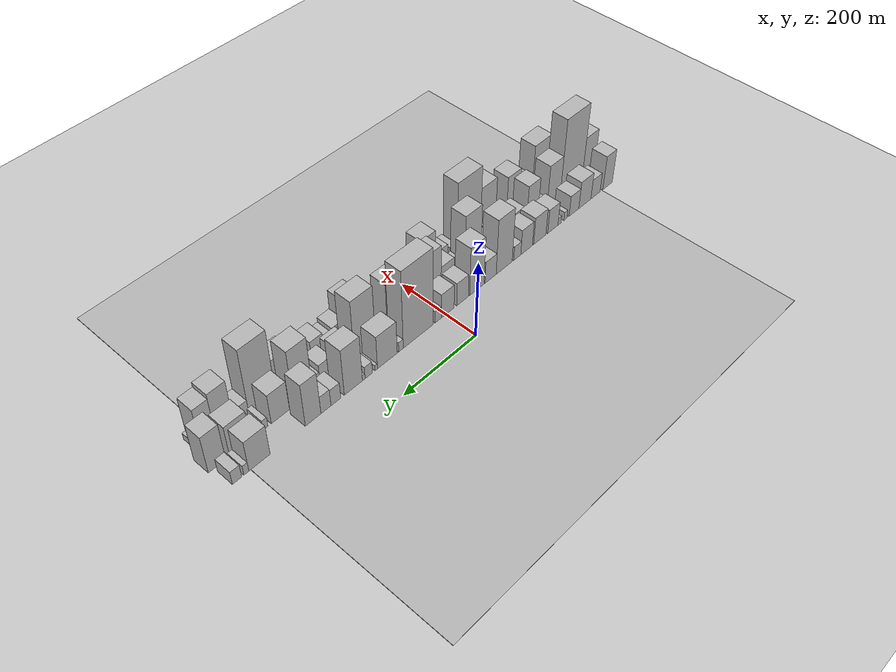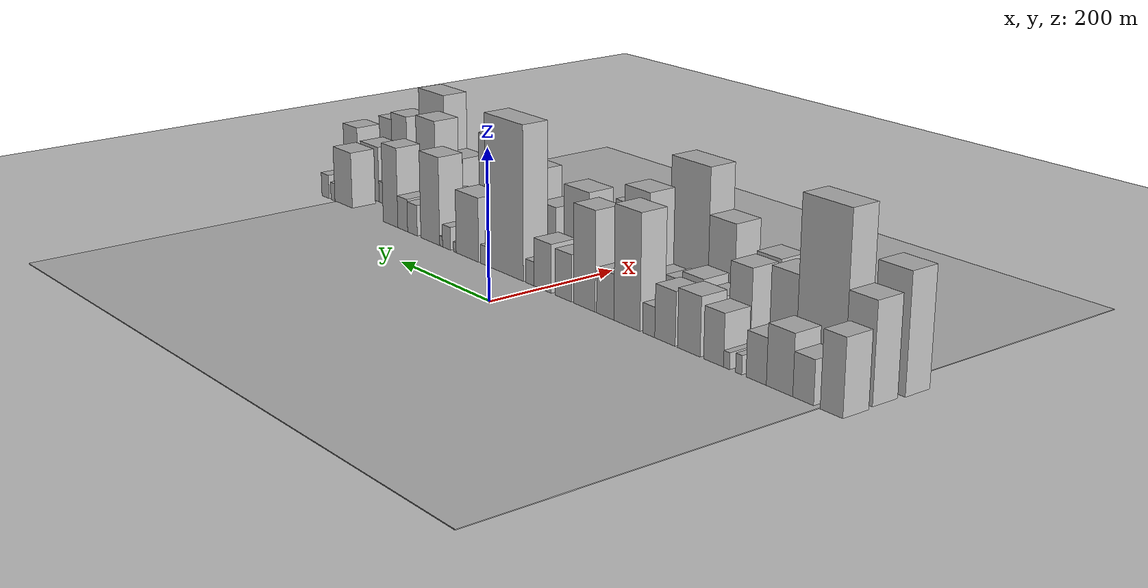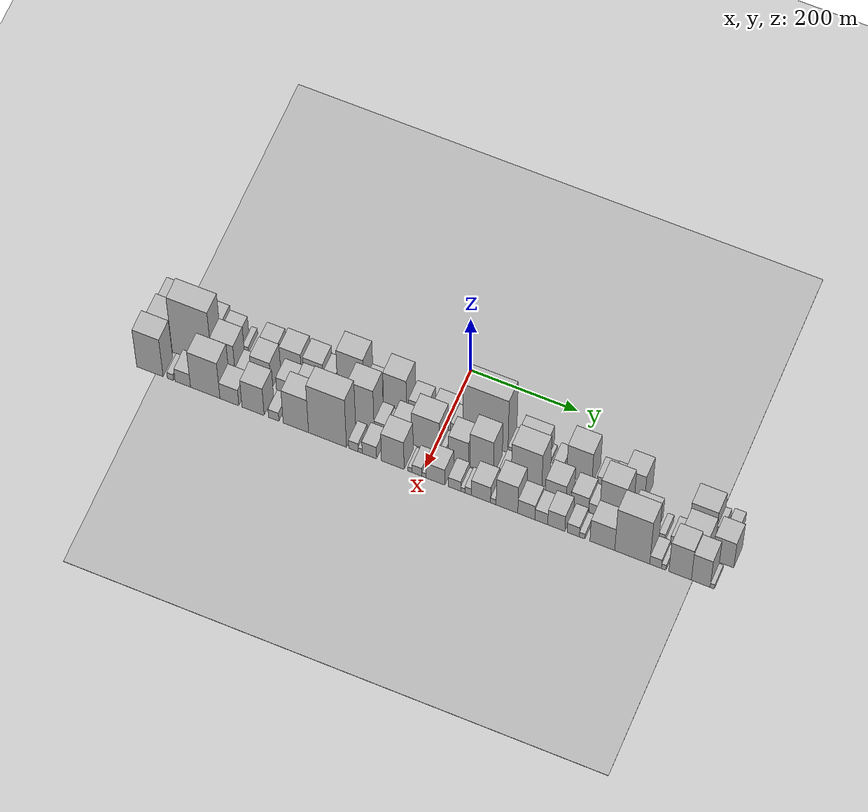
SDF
<?xml version="1.0" encoding="utf-8"?>

<sdf version="1.6">

   <world name="default">

      <gui fullscreen="0">

         <camera name="user_camera">

            <pose>-15 0 4.57585 0 0 0</pose>

            <view_controller>orbit</view_controller>

         </camera>

      </gui>

      <scene>

         <sky>

           <clouds>

             <speed>12</speed>

           </clouds>

         </sky>

         <ambient>0.4 0.4 0.4 1</ambient>

         <background>0.7 0.7 0.7 1</background>

         <shadows>1</shadows>

      </scene>

      <gravity>0 0 -9.8066</gravity>

      <magnetic_field>6e-06 2.3e-05 -4.2e-05</magnetic_field>

      <physics default="0" name="default_physics" type="ode">

         <ode>

            <solver>

               <type>quick</type>

               <iters>10</iters>

               <sor>1.0</sor>

               <use_dynamic_moi_rescaling>0</use_dynamic_moi_rescaling>

            </solver>

            <constraints>

               <cfm>0</cfm>

               <erp>0.2</erp>

               <contact_max_correcting_vel>100</contact_max_correcting_vel>

               <contact_surface_layer>0.001</contact_surface_layer>

            </constraints>

         </ode>

         <max_step_size>0.004</max_step_size>

         <real_time_factor>1</real_time_factor>

         <real_time_update_rate>250</real_time_update_rate>

      </physics>

      <light name="sun" type="directional">

         <cast_shadows>1</cast_shadows>

         <pose>0 0 10 0 0 0</pose>

         <diffuse>0.8 0.8 0.8 1</diffuse>

         <specular>0.2 0.2 0.2 1</specular>

         <attenuation>

            <range>1000</range>

            <constant>0.9</constant>

            <linear>0.01</linear>

            <quadratic>0.001</quadratic>

         </attenuation>

         <direction>-0.5 0.1 -0.9</direction>

      </light>

      <include>

         <name>ground_plane_1</name>

         <uri>model://HANNAS_ground_plane</uri>

         <pose>0 0 0  0 0 0</pose>

      </include>

      <include>

         <name>ground_plane_2</name>

         <uri>model://HANNAS_ground_plane</uri>

         <pose>100 0 0  0 0 0</pose>

      </include>

      <model name="building_1">

         <static>1</static>

         <pose frame="">100.0000 -519.0845 0 0.000000 0.000000 0.000000</pose>

         <link name="link">

            <pose frame="">0 0 46.50 0 0 0</pose>

            <collision name="collision">

               <geometry>

                  <box>

                     <size>40.0000 33.8309 93.0000</size>

                  </box>

               </geometry>

               <max_contacts>10</max_contacts>

               <surface>

                  <contact>

                     <ode/>

                  </contact>

                  <bounce/>

                  <friction>

                     <torsional>

                        <ode/>

                     </torsional>

                     <ode/>

                  </friction>

               </surface>

            </collision>

            <visual name="visual">

               <cast_shadows>0</cast_shadows>

               <geometry>

                  <box>

                     <size>40.0000 33.8309 93.0000</size>

                  </box>

               </geometry>

               <material>

                  <script>

                     <uri>model://HANNAS_wall/materials/scripts</uri>

                     <uri>model://HANNAS_wall/materials/textures</uri>

                     <name>vrc/HANNAS_wall</name>

                  </script>

               </material>

            </visual>

            <self_collide>0</self_collide>

            <enable_wind>0</enable_wind>

            <kinematic>0</kinematic>

         </link>

      </model>

      <model name="building_2">

         <static>1</static>

         <pose frame="">100.0000 -476.1004 0 0.000000 0.000000 0.000000</pose>

         <link name="link">

            <pose frame="">0 0 27.00 0 0 0</pose>

            <collision name="collision">

               <geometry>

                  <box>

                     <size>40.0000 32.1374 54.0000</size>

                  </box>

               </geometry>

               <max_contacts>10</max_contacts>

               <surface>

                  <contact>

                     <ode/>

                  </contact>

                  <bounce/>

                  <friction>

                     <torsional>

                        <ode/>

                     </torsional>

                     <ode/>

                  </friction>

               </surface>

            </collision>

            <visual name="visual">

               <cast_shadows>0</cast_shadows>

               <geometry>

                  <box>

                     <size>40.0000 32.1374 54.0000</size>

                  </box>

               </geometry>

               <material>

                  <script>

                     <uri>model://HANNAS_wall/materials/scripts</uri>

                     <uri>model://HANNAS_wall/materials/textures</uri>

                     <name>vrc/HANNAS_wall</name>

                  </script>

               </material>

            </visual>

            <self_collide>0</self_collide>

            <enable_wind>0</enable_wind>

            <kinematic>0</kinematic>

         </link>

      </model>

      <model name="building_3">

         <static>1</static>

         <pose frame="">100.0000 -439.1285 0 0.000000 0.000000 0.000000</pose>

         <link name="link">

            <pose frame="">0 0 37.50 0 0 0</pose>

            <collision name="collision">

               <geometry>

                  <box>

                     <size>40.0000 41.8063 75.0000</size>

                  </box>

               </geometry>

               <max_contacts>10</max_contacts>

               <surface>

                  <contact>

                     <ode/>

                  </contact>

                  <bounce/>

                  <friction>

                     <torsional>

                        <ode/>

                     </torsional>

                     <ode/>

                  </friction>

               </surface>

            </collision>

            <visual name="visual">

               <cast_shadows>0</cast_shadows>

               <geometry>

                  <box>

                     <size>40.0000 41.8063 75.0000</size>

                  </box>

               </geometry>

               <material>

                  <script>

                     <uri>model://HANNAS_wall/materials/scripts</uri>

                     <uri>model://HANNAS_wall/materials/textures</uri>

                     <name>vrc/HANNAS_wall</name>

                  </script>

               </material>

            </visual>

            <self_collide>0</self_collide>

            <enable_wind>0</enable_wind>

            <kinematic>0</kinematic>

         </link>

      </model>

      <model name="building_4">

         <static>1</static>

         <pose frame="">100.0000 -401.7499 0 0.000000 0.000000 0.000000</pose>

         <link name="link">

            <pose frame="">0 0 28.50 0 0 0</pose>

            <collision name="collision">

               <geometry>

                  <box>

                     <size>40.0000 32.9508 57.0000</size>

                  </box>

               </geometry>

               <max_contacts>10</max_contacts>

               <surface>

                  <contact>

                     <ode/>

                  </contact>

                  <bounce/>

                  <friction>

                     <torsional>

                        <ode/>

                     </torsional>

                     <ode/>

                  </friction>

               </surface>

            </collision>

            <visual name="visual">

               <cast_shadows>0</cast_shadows>

               <geometry>

                  <box>

                     <size>40.0000 32.9508 57.0000</size>

                  </box>

               </geometry>

               <material>

                  <script>

                     <uri>model://HANNAS_wall/materials/scripts</uri>

                     <uri>model://HANNAS_wall/materials/textures</uri>

                     <name>vrc/HANNAS_wall</name>

                  </script>

               </material>

            </visual>

            <self_collide>0</self_collide>

            <enable_wind>0</enable_wind>

            <kinematic>0</kinematic>

         </link>

      </model>

      <model name="building_5">

         <static>1</static>

         <pose frame="">100.0000 -373.0983 0 0.000000 0.000000 0.000000</pose>

         <link name="link">

            <pose frame="">0 0 12.00 0 0 0</pose>

            <collision name="collision">

               <geometry>

                  <box>

                     <size>40.0000 10.3525 24.0000</size>

                  </box>

               </geometry>

               <max_contacts>10</max_contacts>

               <surface>

                  <contact>

                     <ode/>

                  </contact>

                  <bounce/>

                  <friction>

                     <torsional>

                        <ode/>

                     </torsional>

                     <ode/>

                  </friction>

               </surface>

            </collision>

            <visual name="visual">

               <cast_shadows>0</cast_shadows>

               <geometry>

                  <box>

                     <size>40.0000 10.3525 24.0000</size>

                  </box>

               </geometry>

               <material>

                  <script>

                     <uri>model://HANNAS_wall/materials/scripts</uri>

                     <uri>model://HANNAS_wall/materials/textures</uri>

                     <name>vrc/HANNAS_wall</name>

                  </script>

               </material>

            </visual>

            <self_collide>0</self_collide>

            <enable_wind>0</enable_wind>

            <kinematic>0</kinematic>

         </link>

      </model>

      <model name="building_6">

         <static>1</static>

         <pose frame="">100.0000 -352.8675 0 0.000000 0.000000 0.000000</pose>

         <link name="link">

            <pose frame="">0 0 10.50 0 0 0</pose>

            <collision name="collision">

               <geometry>

                  <box>

                     <size>40.0000 10.1091 21.0000</size>

                  </box>

               </geometry>

               <max_contacts>10</max_contacts>

               <surface>

                  <contact>

                     <ode/>

                  </contact>

                  <bounce/>

                  <friction>

                     <torsional>

                        <ode/>

                     </torsional>

                     <ode/>

                  </friction>

               </surface>

            </collision>

            <visual name="visual">

               <cast_shadows>0</cast_shadows>

               <geometry>

                  <box>

                     <size>40.0000 10.1091 21.0000</size>

                  </box>

               </geometry>

               <material>

                  <script>

                     <uri>model://HANNAS_wall/materials/scripts</uri>

                     <uri>model://HANNAS_wall/materials/textures</uri>

                     <name>vrc/HANNAS_wall</name>

                  </script>

               </material>

            </visual>

            <self_collide>0</self_collide>

            <enable_wind>0</enable_wind>

            <kinematic>0</kinematic>

         </link>

      </model>

      <model name="building_7">

         <static>1</static>

         <pose frame="">100.0000 -330.7719 0 0.000000 0.000000 0.000000</pose>

         <link name="link">

            <pose frame="">0 0 33.00 0 0 0</pose>

            <collision name="collision">

               <geometry>

                  <box>

                     <size>40.0000 34.0822 66.0000</size>

                  </box>

               </geometry>

               <max_contacts>10</max_contacts>

               <surface>

                  <contact>

                     <ode/>

                  </contact>

                  <bounce/>

                  <friction>

                     <torsional>

                        <ode/>

                     </torsional>

                     <ode/>

                  </friction>

               </surface>

            </collision>

            <visual name="visual">

               <cast_shadows>0</cast_shadows>

               <geometry>

                  <box>

                     <size>40.0000 34.0822 66.0000</size>

                  </box>

               </geometry>

               <material>

                  <script>

                     <uri>model://HANNAS_wall/materials/scripts</uri>

                     <uri>model://HANNAS_wall/materials/textures</uri>

                     <name>vrc/HANNAS_wall</name>

                  </script>

               </material>

            </visual>

            <self_collide>0</self_collide>

            <enable_wind>0</enable_wind>

            <kinematic>0</kinematic>

         </link>

      </model>

      <model name="building_8">

         <static>1</static>

         <pose frame="">100.0000 -287.7818 0 0.000000 0.000000 0.000000</pose>

         <link name="link">

            <pose frame="">0 0 37.50 0 0 0</pose>

            <collision name="collision">

               <geometry>

                  <box>

                     <size>40.0000 39.8979 75.0000</size>

                  </box>

               </geometry>

               <max_contacts>10</max_contacts>

               <surface>

                  <contact>

                     <ode/>

                  </contact>

                  <bounce/>

                  <friction>

                     <torsional>

                        <ode/>

                     </torsional>

                     <ode/>

                  </friction>

               </surface>

            </collision>

            <visual name="visual">

               <cast_shadows>0</cast_shadows>

               <geometry>

                  <box>

                     <size>40.0000 39.8979 75.0000</size>

                  </box>

               </geometry>

               <material>

                  <script>

                     <uri>model://HANNAS_wall/materials/scripts</uri>

                     <uri>model://HANNAS_wall/materials/textures</uri>

                     <name>vrc/HANNAS_wall</name>

                  </script>

               </material>

            </visual>

            <self_collide>0</self_collide>

            <enable_wind>0</enable_wind>

            <kinematic>0</kinematic>

         </link>

      </model>

      <model name="building_9">

         <static>1</static>

         <pose frame="">100.0000 -245.2879 0 0.000000 0.000000 0.000000</pose>

         <link name="link">

            <pose frame="">0 0 34.50 0 0 0</pose>

            <collision name="collision">

               <geometry>

                  <box>

                     <size>40.0000 37.0899 69.0000</size>

                  </box>

               </geometry>

               <max_contacts>10</max_contacts>

               <surface>

                  <contact>

                     <ode/>

                  </contact>

                  <bounce/>

                  <friction>

                     <torsional>

                        <ode/>

                     </torsional>

                     <ode/>

                  </friction>

               </surface>

            </collision>

            <visual name="visual">

               <cast_shadows>0</cast_shadows>

               <geometry>

                  <box>

                     <size>40.0000 37.0899 69.0000</size>

                  </box>

               </geometry>

               <material>

                  <script>

                     <uri>model://HANNAS_wall/materials/scripts</uri>

                     <uri>model://HANNAS_wall/materials/textures</uri>

                     <name>vrc/HANNAS_wall</name>

                  </script>

               </material>

            </visual>

            <self_collide>0</self_collide>

            <enable_wind>0</enable_wind>

            <kinematic>0</kinematic>

         </link>

      </model>

      <model name="building_10">

         <static>1</static>

         <pose frame="">100.0000 -215.5935 0 0.000000 0.000000 0.000000</pose>

         <link name="link">

            <pose frame="">0 0 19.50 0 0 0</pose>

            <collision name="collision">

               <geometry>

                  <box>

                     <size>40.0000 22.2987 39.0000</size>

                  </box>

               </geometry>

               <max_contacts>10</max_contacts>

               <surface>

                  <contact>

                     <ode/>

                  </contact>

                  <bounce/>

                  <friction>

                     <torsional>

                        <ode/>

                     </torsional>

                     <ode/>

                  </friction>

               </surface>

            </collision>

            <visual name="visual">

               <cast_shadows>0</cast_shadows>

               <geometry>

                  <box>

                     <size>40.0000 22.2987 39.0000</size>

                  </box>

               </geometry>

               <material>

                  <script>

                     <uri>model://HANNAS_wall/materials/scripts</uri>

                     <uri>model://HANNAS_wall/materials/textures</uri>

                     <name>vrc/HANNAS_wall</name>

                  </script>

               </material>

            </visual>

            <self_collide>0</self_collide>

            <enable_wind>0</enable_wind>

            <kinematic>0</kinematic>

         </link>

      </model>

      <model name="building_11">

         <static>1</static>

         <pose frame="">100.0000 -174.6152 0 0.000000 0.000000 0.000000</pose>

         <link name="link">

            <pose frame="">0 0 75.00 0 0 0</pose>

            <collision name="collision">

               <geometry>

                  <box>

                     <size>40.0000 49.6580 150.0000</size>

                  </box>

               </geometry>

               <max_contacts>10</max_contacts>

               <surface>

                  <contact>

                     <ode/>

                  </contact>

                  <bounce/>

                  <friction>

                     <torsional>

                        <ode/>

                     </torsional>

                     <ode/>

                  </friction>

               </surface>

            </collision>

            <visual name="visual">

               <cast_shadows>0</cast_shadows>

               <geometry>

                  <box>

                     <size>40.0000 49.6580 150.0000</size>

                  </box>

               </geometry>

               <material>

                  <script>

                     <uri>model://HANNAS_wall/materials/scripts</uri>

                     <uri>model://HANNAS_wall/materials/textures</uri>

                     <name>vrc/HANNAS_wall</name>

                  </script>

               </material>

            </visual>

            <self_collide>0</self_collide>

            <enable_wind>0</enable_wind>

            <kinematic>0</kinematic>

         </link>

      </model>

      <model name="building_12">

         <static>1</static>

         <pose frame="">100.0000 -132.8719 0 0.000000 0.000000 0.000000</pose>

         <link name="link">

            <pose frame="">0 0 30.00 0 0 0</pose>

            <collision name="collision">

               <geometry>

                  <box>

                     <size>40.0000 33.8285 60.0000</size>

                  </box>

               </geometry>

               <max_contacts>10</max_contacts>

               <surface>

                  <contact>

                     <ode/>

                  </contact>

                  <bounce/>

                  <friction>

                     <torsional>

                        <ode/>

                     </torsional>

                     <ode/>

                  </friction>

               </surface>

            </collision>

            <visual name="visual">

               <cast_shadows>0</cast_shadows>

               <geometry>

                  <box>

                     <size>40.0000 33.8285 60.0000</size>

                  </box>

               </geometry>

               <material>

                  <script>

                     <uri>model://HANNAS_wall/materials/scripts</uri>

                     <uri>model://HANNAS_wall/materials/textures</uri>

                     <name>vrc/HANNAS_wall</name>

                  </script>

               </material>

            </visual>

            <self_collide>0</self_collide>

            <enable_wind>0</enable_wind>

            <kinematic>0</kinematic>

         </link>

      </model>

      <model name="building_13">

         <static>1</static>

         <pose frame="">100.0000 -91.4328 0 0.000000 0.000000 0.000000</pose>

         <link name="link">

            <pose frame="">0 0 66.00 0 0 0</pose>

            <collision name="collision">

               <geometry>

                  <box>

                     <size>40.0000 43.0498 132.0000</size>

                  </box>

               </geometry>

               <max_contacts>10</max_contacts>

               <surface>

                  <contact>

                     <ode/>

                  </contact>

                  <bounce/>

                  <friction>

                     <torsional>

                        <ode/>

                     </torsional>

                     <ode/>

                  </friction>

               </surface>

            </collision>

            <visual name="visual">

               <cast_shadows>0</cast_shadows>

               <geometry>

                  <box>

                     <size>40.0000 43.0498 132.0000</size>

                  </box>

               </geometry>

               <material>

                  <script>

                     <uri>model://HANNAS_wall/materials/scripts</uri>

                     <uri>model://HANNAS_wall/materials/textures</uri>

                     <name>vrc/HANNAS_wall</name>

                  </script>

               </material>

            </visual>

            <self_collide>0</self_collide>

            <enable_wind>0</enable_wind>

            <kinematic>0</kinematic>

         </link>

      </model>

      <model name="building_14">

         <static>1</static>

         <pose frame="">100.0000 -48.8827 0 0.000000 0.000000 0.000000</pose>

         <link name="link">

            <pose frame="">0 0 31.50 0 0 0</pose>

            <collision name="collision">

               <geometry>

                  <box>

                     <size>40.0000 34.0503 63.0000</size>

                  </box>

               </geometry>

               <max_contacts>10</max_contacts>

               <surface>

                  <contact>

                     <ode/>

                  </contact>

                  <bounce/>

                  <friction>

                     <torsional>

                        <ode/>

                     </torsional>

                     <ode/>

                  </friction>

               </surface>

            </collision>

            <visual name="visual">

               <cast_shadows>0</cast_shadows>

               <geometry>

                  <box>

                     <size>40.0000 34.0503 63.0000</size>

                  </box>

               </geometry>

               <material>

                  <script>

                     <uri>model://HANNAS_wall/materials/scripts</uri>

                     <uri>model://HANNAS_wall/materials/textures</uri>

                     <name>vrc/HANNAS_wall</name>

                  </script>

               </material>

            </visual>

            <self_collide>0</self_collide>

            <enable_wind>0</enable_wind>

            <kinematic>0</kinematic>

         </link>

      </model>

      <model name="building_15">

         <static>1</static>

         <pose frame="">100.0000 -5.6149 0 0.000000 0.000000 0.000000</pose>

         <link name="link">

            <pose frame="">0 0 33.00 0 0 0</pose>

            <collision name="collision">

               <geometry>

                  <box>

                     <size>40.0000 36.4854 66.0000</size>

                  </box>

               </geometry>

               <max_contacts>10</max_contacts>

               <surface>

                  <contact>

                     <ode/>

                  </contact>

                  <bounce/>

                  <friction>

                     <torsional>

                        <ode/>

                     </torsional>

                     <ode/>

                  </friction>

               </surface>

            </collision>

            <visual name="visual">

               <cast_shadows>0</cast_shadows>

               <geometry>

                  <box>

                     <size>40.0000 36.4854 66.0000</size>

                  </box>

               </geometry>

               <material>

                  <script>

                     <uri>model://HANNAS_wall/materials/scripts</uri>

                     <uri>model://HANNAS_wall/materials/textures</uri>

                     <name>vrc/HANNAS_wall</name>

                  </script>

               </material>

            </visual>

            <self_collide>0</self_collide>

            <enable_wind>0</enable_wind>

            <kinematic>0</kinematic>

         </link>

      </model>

      <model name="building_16">

         <static>1</static>

         <pose frame="">100.0000 21.5906 0 0.000000 0.000000 0.000000</pose>

         <link name="link">

            <pose frame="">0 0 16.50 0 0 0</pose>

            <collision name="collision">

               <geometry>

                  <box>

                     <size>40.0000 17.9257 33.0000</size>

                  </box>

               </geometry>

               <max_contacts>10</max_contacts>

               <surface>

                  <contact>

                     <ode/>

                  </contact>

                  <bounce/>

                  <friction>

                     <torsional>

                        <ode/>

                     </torsional>

                     <ode/>

                  </friction>

               </surface>

            </collision>

            <visual name="visual">

               <cast_shadows>0</cast_shadows>

               <geometry>

                  <box>

                     <size>40.0000 17.9257 33.0000</size>

                  </box>

               </geometry>

               <material>

                  <script>

                     <uri>model://HANNAS_wall/materials/scripts</uri>

                     <uri>model://HANNAS_wall/materials/textures</uri>

                     <name>vrc/HANNAS_wall</name>

                  </script>

               </material>

            </visual>

            <self_collide>0</self_collide>

            <enable_wind>0</enable_wind>

            <kinematic>0</kinematic>

         </link>

      </model>

      <model name="building_17">

         <static>1</static>

         <pose frame="">100.0000 77.3882 0 0.000000 0.000000 0.000000</pose>

         <link name="link">

            <pose frame="">0 0 105.00 0 0 0</pose>

            <collision name="collision">

               <geometry>

                  <box>

                     <size>40.0000 83.6695 210.0000</size>

                  </box>

               </geometry>

               <max_contacts>10</max_contacts>

               <surface>

                  <contact>

                     <ode/>

                  </contact>

                  <bounce/>

                  <friction>

                     <torsional>

                        <ode/>

                     </torsional>

                     <ode/>

                  </friction>

               </surface>

            </collision>

            <visual name="visual">

               <cast_shadows>0</cast_shadows>

               <geometry>

                  <box>

                     <size>40.0000 83.6695 210.0000</size>

                  </box>

               </geometry>

               <material>

                  <script>

                     <uri>model://HANNAS_wall/materials/scripts</uri>

                     <uri>model://HANNAS_wall/materials/textures</uri>

                     <name>vrc/HANNAS_wall</name>

                  </script>

               </material>

            </visual>

            <self_collide>0</self_collide>

            <enable_wind>0</enable_wind>

            <kinematic>0</kinematic>

         </link>

      </model>

      <model name="building_18">

         <static>1</static>

         <pose frame="">100.0000 125.5073 0 0.000000 0.000000 0.000000</pose>

         <link name="link">

            <pose frame="">0 0 13.50 0 0 0</pose>

            <collision name="collision">

               <geometry>

                  <box>

                     <size>40.0000 12.5687 27.0000</size>

                  </box>

               </geometry>

               <max_contacts>10</max_contacts>

               <surface>

                  <contact>

                     <ode/>

                  </contact>

                  <bounce/>

                  <friction>

                     <torsional>

                        <ode/>

                     </torsional>

                     <ode/>

                  </friction>

               </surface>

            </collision>

            <visual name="visual">

               <cast_shadows>0</cast_shadows>

               <geometry>

                  <box>

                     <size>40.0000 12.5687 27.0000</size>

                  </box>

               </geometry>

               <material>

                  <script>

                     <uri>model://HANNAS_wall/materials/scripts</uri>

                     <uri>model://HANNAS_wall/materials/textures</uri>

                     <name>vrc/HANNAS_wall</name>

                  </script>

               </material>

            </visual>

            <self_collide>0</self_collide>

            <enable_wind>0</enable_wind>

            <kinematic>0</kinematic>

         </link>

      </model>

      <model name="building_19">

         <static>1</static>

         <pose frame="">100.0000 162.1623 0 0.000000 0.000000 0.000000</pose>

         <link name="link">

            <pose frame="">0 0 45.00 0 0 0</pose>

            <collision name="collision">

               <geometry>

                  <box>

                     <size>40.0000 52.7413 90.0000</size>

                  </box>

               </geometry>

               <max_contacts>10</max_contacts>

               <surface>

                  <contact>

                     <ode/>

                  </contact>

                  <bounce/>

                  <friction>

                     <torsional>

                        <ode/>

                     </torsional>

                     <ode/>

                  </friction>

               </surface>

            </collision>

            <visual name="visual">

               <cast_shadows>0</cast_shadows>

               <geometry>

                  <box>

                     <size>40.0000 52.7413 90.0000</size>

                  </box>

               </geometry>

               <material>

                  <script>

                     <uri>model://HANNAS_wall/materials/scripts</uri>

                     <uri>model://HANNAS_wall/materials/textures</uri>

                     <name>vrc/HANNAS_wall</name>

                  </script>

               </material>

            </visual>

            <self_collide>0</self_collide>

            <enable_wind>0</enable_wind>

            <kinematic>0</kinematic>

         </link>

      </model>

      <model name="building_20">

         <static>1</static>

         <pose frame="">100.0000 191.7754 0 0.000000 0.000000 0.000000</pose>

         <link name="link">

            <pose frame="">0 0 7.50 0 0 0</pose>

            <collision name="collision">

               <geometry>

                  <box>

                     <size>40.0000 6.4849 15.0000</size>

                  </box>

               </geometry>

               <max_contacts>10</max_contacts>

               <surface>

                  <contact>

                     <ode/>

                  </contact>

                  <bounce/>

                  <friction>

                     <torsional>

                        <ode/>

                     </torsional>

                     <ode/>

                  </friction>

               </surface>

            </collision>

            <visual name="visual">

               <cast_shadows>0</cast_shadows>

               <geometry>

                  <box>

                     <size>40.0000 6.4849 15.0000</size>

                  </box>

               </geometry>

               <material>

                  <script>

                     <uri>model://HANNAS_wall/materials/scripts</uri>

                     <uri>model://HANNAS_wall/materials/textures</uri>

                     <name>vrc/HANNAS_wall</name>

                  </script>

               </material>

            </visual>

            <self_collide>0</self_collide>

            <enable_wind>0</enable_wind>

            <kinematic>0</kinematic>

         </link>

      </model>

      <model name="building_21">

         <static>1</static>

         <pose frame="">100.0000 211.6405 0 0.000000 0.000000 0.000000</pose>

         <link name="link">

            <pose frame="">0 0 16.50 0 0 0</pose>

            <collision name="collision">

               <geometry>

                  <box>

                     <size>40.0000 19.2453 33.0000</size>

                  </box>

               </geometry>

               <max_contacts>10</max_contacts>

               <surface>

                  <contact>

                     <ode/>

                  </contact>

                  <bounce/>

                  <friction>

                     <torsional>

                        <ode/>

                     </torsional>

                     <ode/>

                  </friction>

               </surface>

            </collision>

            <visual name="visual">

               <cast_shadows>0</cast_shadows>

               <geometry>

                  <box>

                     <size>40.0000 19.2453 33.0000</size>

                  </box>

               </geometry>

               <material>

                  <script>

                     <uri>model://HANNAS_wall/materials/scripts</uri>

                     <uri>model://HANNAS_wall/materials/textures</uri>

                     <name>vrc/HANNAS_wall</name>

                  </script>

               </material>

            </visual>

            <self_collide>0</self_collide>

            <enable_wind>0</enable_wind>

            <kinematic>0</kinematic>

         </link>

      </model>

      <model name="building_22">

         <static>1</static>

         <pose frame="">100.0000 224.7360 0 0.000000 0.000000 0.000000</pose>

         <link name="link">

            <pose frame="">0 0 7.50 0 0 0</pose>

            <collision name="collision">

               <geometry>

                  <box>

                     <size>40.0000 6.9459 15.0000</size>

                  </box>

               </geometry>

               <max_contacts>10</max_contacts>

               <surface>

                  <contact>

                     <ode/>

                  </contact>

                  <bounce/>

                  <friction>

                     <torsional>

                        <ode/>

                     </torsional>

                     <ode/>

                  </friction>

               </surface>

            </collision>

            <visual name="visual">

               <cast_shadows>0</cast_shadows>

               <geometry>

                  <box>

                     <size>40.0000 6.9459 15.0000</size>

                  </box>

               </geometry>

               <material>

                  <script>

                     <uri>model://HANNAS_wall/materials/scripts</uri>

                     <uri>model://HANNAS_wall/materials/textures</uri>

                     <name>vrc/HANNAS_wall</name>

                  </script>

               </material>

            </visual>

            <self_collide>0</self_collide>

            <enable_wind>0</enable_wind>

            <kinematic>0</kinematic>

         </link>

      </model>

      <model name="building_23">

         <static>1</static>

         <pose frame="">100.0000 251.5216 0 0.000000 0.000000 0.000000</pose>

         <link name="link">

            <pose frame="">0 0 63.00 0 0 0</pose>

            <collision name="collision">

               <geometry>

                  <box>

                     <size>40.0000 46.6253 126.0000</size>

                  </box>

               </geometry>

               <max_contacts>10</max_contacts>

               <surface>

                  <contact>

                     <ode/>

                  </contact>

                  <bounce/>

                  <friction>

                     <torsional>

                        <ode/>

                     </torsional>

                     <ode/>

                  </friction>

               </surface>

            </collision>

            <visual name="visual">

               <cast_shadows>0</cast_shadows>

               <geometry>

                  <box>

                     <size>40.0000 46.6253 126.0000</size>

                  </box>

               </geometry>

               <material>

                  <script>

                     <uri>model://HANNAS_wall/materials/scripts</uri>

                     <uri>model://HANNAS_wall/materials/textures</uri>

                     <name>vrc/HANNAS_wall</name>

                  </script>

               </material>

            </visual>

            <self_collide>0</self_collide>

            <enable_wind>0</enable_wind>

            <kinematic>0</kinematic>

         </link>

      </model>

      <model name="building_24">

         <static>1</static>

         <pose frame="">100.0000 296.1276 0 0.000000 0.000000 0.000000</pose>

         <link name="link">

            <pose frame="">0 0 22.50 0 0 0</pose>

            <collision name="collision">

               <geometry>

                  <box>

                     <size>40.0000 24.5866 45.0000</size>

                  </box>

               </geometry>

               <max_contacts>10</max_contacts>

               <surface>

                  <contact>

                     <ode/>

                  </contact>

                  <bounce/>

                  <friction>

                     <torsional>

                        <ode/>

                     </torsional>

                     <ode/>

                  </friction>

               </surface>

            </collision>

            <visual name="visual">

               <cast_shadows>0</cast_shadows>

               <geometry>

                  <box>

                     <size>40.0000 24.5866 45.0000</size>

                  </box>

               </geometry>

               <material>

                  <script>

                     <uri>model://HANNAS_wall/materials/scripts</uri>

                     <uri>model://HANNAS_wall/materials/textures</uri>

                     <name>vrc/HANNAS_wall</name>

                  </script>

               </material>

            </visual>

            <self_collide>0</self_collide>

            <enable_wind>0</enable_wind>

            <kinematic>0</kinematic>

         </link>

      </model>

      <model name="building_25">

         <static>1</static>

         <pose frame="">100.0000 320.8826 0 0.000000 0.000000 0.000000</pose>

         <link name="link">

            <pose frame="">0 0 24.00 0 0 0</pose>

            <collision name="collision">

               <geometry>

                  <box>

                     <size>40.0000 24.9234 48.0000</size>

                  </box>

               </geometry>

               <max_contacts>10</max_contacts>

               <surface>

                  <contact>

                     <ode/>

                  </contact>

                  <bounce/>

                  <friction>

                     <torsional>

                        <ode/>

                     </torsional>

                     <ode/>

                  </friction>

               </surface>

            </collision>

            <visual name="visual">

               <cast_shadows>0</cast_shadows>

               <geometry>

                  <box>

                     <size>40.0000 24.9234 48.0000</size>

                  </box>

               </geometry>

               <material>

                  <script>

                     <uri>model://HANNAS_wall/materials/scripts</uri>

                     <uri>model://HANNAS_wall/materials/textures</uri>

                     <name>vrc/HANNAS_wall</name>

                  </script>

               </material>

            </visual>

            <self_collide>0</self_collide>

            <enable_wind>0</enable_wind>

            <kinematic>0</kinematic>

         </link>

      </model>

      <model name="building_26">

         <static>1</static>

         <pose frame="">100.0000 352.5367 0 0.000000 0.000000 0.000000</pose>

         <link name="link">

            <pose frame="">0 0 58.50 0 0 0</pose>

            <collision name="collision">

               <geometry>

                  <box>

                     <size>40.0000 38.3847 117.0000</size>

                  </box>

               </geometry>

               <max_contacts>10</max_contacts>

               <surface>

                  <contact>

                     <ode/>

                  </contact>

                  <bounce/>

                  <friction>

                     <torsional>

                        <ode/>

                     </torsional>

                     <ode/>

                  </friction>

               </surface>

            </collision>

            <visual name="visual">

               <cast_shadows>0</cast_shadows>

               <geometry>

                  <box>

                     <size>40.0000 38.3847 117.0000</size>

                  </box>

               </geometry>

               <material>

                  <script>

                     <uri>model://HANNAS_wall/materials/scripts</uri>

                     <uri>model://HANNAS_wall/materials/textures</uri>

                     <name>vrc/HANNAS_wall</name>

                  </script>

               </material>

            </visual>

            <self_collide>0</self_collide>

            <enable_wind>0</enable_wind>

            <kinematic>0</kinematic>

         </link>

      </model>

      <model name="building_27">

         <static>1</static>

         <pose frame="">100.0000 480.1514 0 0.000000 0.000000 0.000000</pose>

         <link name="link">

            <pose frame="">0 0 42.00 0 0 0</pose>

            <collision name="collision">

               <geometry>

                  <box>

                     <size>40.0000 48.9483 84.0000</size>

                  </box>

               </geometry>

               <max_contacts>10</max_contacts>

               <surface>

                  <contact>

                     <ode/>

                  </contact>

                  <bounce/>

                  <friction>

                     <torsional>

                        <ode/>

                     </torsional>

                     <ode/>

                  </friction>

               </surface>

            </collision>

            <visual name="visual">

               <cast_shadows>0</cast_shadows>

               <geometry>

                  <box>

                     <size>40.0000 48.9483 84.0000</size>

                  </box>

               </geometry>

               <material>

                  <script>

                     <uri>model://HANNAS_wall/materials/scripts</uri>

                     <uri>model://HANNAS_wall/materials/textures</uri>

                     <name>vrc/HANNAS_wall</name>

                  </script>

               </material>

            </visual>

            <self_collide>0</self_collide>

            <enable_wind>0</enable_wind>

            <kinematic>0</kinematic>

         </link>

      </model>

      <model name="building_28">

         <static>1</static>

         <pose frame="">100.0000 510.3059 0 0.000000 0.000000 0.000000</pose>

         <link name="link">

            <pose frame="">0 0 13.50 0 0 0</pose>

            <collision name="collision">

               <geometry>

                  <box>

                     <size>40.0000 11.3608 27.0000</size>

                  </box>

               </geometry>

               <max_contacts>10</max_contacts>

               <surface>

                  <contact>

                     <ode/>

                  </contact>

                  <bounce/>

                  <friction>

                     <torsional>

                        <ode/>

                     </torsional>

                     <ode/>

                  </friction>

               </surface>

            </collision>

            <visual name="visual">

               <cast_shadows>0</cast_shadows>

               <geometry>

                  <box>

                     <size>40.0000 11.3608 27.0000</size>

                  </box>

               </geometry>

               <material>

                  <script>

                     <uri>model://HANNAS_wall/materials/scripts</uri>

                     <uri>model://HANNAS_wall/materials/textures</uri>

                     <name>vrc/HANNAS_wall</name>

                  </script>

               </material>

            </visual>

            <self_collide>0</self_collide>

            <enable_wind>0</enable_wind>

            <kinematic>0</kinematic>

         </link>

      </model>

      <model name="building_29">

         <static>1</static>

         <pose frame="">100.0000 531.5163 0 0.000000 0.000000 0.000000</pose>

         <link name="link">

            <pose frame="">0 0 18.00 0 0 0</pose>

            <collision name="collision">

               <geometry>

                  <box>

                     <size>40.0000 21.0600 36.0000</size>

                  </box>

               </geometry>

               <max_contacts>10</max_contacts>

               <surface>

                  <contact>

                     <ode/>

                  </contact>

                  <bounce/>

                  <friction>

                     <torsional>

                        <ode/>

                     </torsional>

                     <ode/>

                  </friction>

               </surface>

            </collision>

            <visual name="visual">

               <cast_shadows>0</cast_shadows>

               <geometry>

                  <box>

                     <size>40.0000 21.0600 36.0000</size>

                  </box>

               </geometry>

               <material>

                  <script>

                     <uri>model://HANNAS_wall/materials/scripts</uri>

                     <uri>model://HANNAS_wall/materials/textures</uri>

                     <name>vrc/HANNAS_wall</name>

                  </script>

               </material>

            </visual>

            <self_collide>0</self_collide>

            <enable_wind>0</enable_wind>

            <kinematic>0</kinematic>

         </link>

      </model>

      <model name="building_30">

         <static>1</static>

         <pose frame="">149.0000 -511.6956 0 0.000000 0.000000 0.000000</pose>

         <link name="link">

            <pose frame="">0 0 61.50 0 0 0</pose>

            <collision name="collision">

               <geometry>

                  <box>

                     <size>40.0000 42.6088 123.0000</size>

                  </box>

               </geometry>

               <max_contacts>10</max_contacts>

               <surface>

                  <contact>

                     <ode/>

                  </contact>

                  <bounce/>

                  <friction>

                     <torsional>

                        <ode/>

                     </torsional>

                     <ode/>

                  </friction>

               </surface>

            </collision>

            <visual name="visual">

               <cast_shadows>0</cast_shadows>

               <geometry>

                  <box>

                     <size>40.0000 42.6088 123.0000</size>

                  </box>

               </geometry>

               <material>

                  <script>

                     <uri>model://HANNAS_wall/materials/scripts</uri>

                     <uri>model://HANNAS_wall/materials/textures</uri>

                     <name>vrc/HANNAS_wall</name>

                  </script>

               </material>

            </visual>

            <self_collide>0</self_collide>

            <enable_wind>0</enable_wind>

            <kinematic>0</kinematic>

         </link>

      </model>

      <model name="building_31">

         <static>1</static>

         <pose frame="">149.0000 -452.3626 0 0.000000 0.000000 0.000000</pose>

         <link name="link">

            <pose frame="">0 0 108.00 0 0 0</pose>

            <collision name="collision">

               <geometry>

                  <box>

                     <size>40.0000 76.0571 216.0000</size>

                  </box>

               </geometry>

               <max_contacts>10</max_contacts>

               <surface>

                  <contact>

                     <ode/>

                  </contact>

                  <bounce/>

                  <friction>

                     <torsional>

                        <ode/>

                     </torsional>

                     <ode/>

                  </friction>

               </surface>

            </collision>

            <visual name="visual">

               <cast_shadows>0</cast_shadows>

               <geometry>

                  <box>

                     <size>40.0000 76.0571 216.0000</size>

                  </box>

               </geometry>

               <material>

                  <script>

                     <uri>model://HANNAS_wall/materials/scripts</uri>

                     <uri>model://HANNAS_wall/materials/textures</uri>

                     <name>vrc/HANNAS_wall</name>

                  </script>

               </material>

            </visual>

            <self_collide>0</self_collide>

            <enable_wind>0</enable_wind>

            <kinematic>0</kinematic>

         </link>

      </model>

      <model name="building_32">

         <static>1</static>

         <pose frame="">149.0000 -392.5495 0 0.000000 0.000000 0.000000</pose>

         <link name="link">

            <pose frame="">0 0 60.00 0 0 0</pose>

            <collision name="collision">

               <geometry>

                  <box>

                     <size>40.0000 43.5690 120.0000</size>

                  </box>

               </geometry>

               <max_contacts>10</max_contacts>

               <surface>

                  <contact>

                     <ode/>

                  </contact>

                  <bounce/>

                  <friction>

                     <torsional>

                        <ode/>

                     </torsional>

                     <ode/>

                  </friction>

               </surface>

            </collision>

            <visual name="visual">

               <cast_shadows>0</cast_shadows>

               <geometry>

                  <box>

                     <size>40.0000 43.5690 120.0000</size>

                  </box>

               </geometry>

               <material>

                  <script>

                     <uri>model://HANNAS_wall/materials/scripts</uri>

                     <uri>model://HANNAS_wall/materials/textures</uri>

                     <name>vrc/HANNAS_wall</name>

                  </script>

               </material>

            </visual>

            <self_collide>0</self_collide>

            <enable_wind>0</enable_wind>

            <kinematic>0</kinematic>

         </link>

      </model>

      <model name="building_33">

         <static>1</static>

         <pose frame="">149.0000 -361.2926 0 0.000000 0.000000 0.000000</pose>

         <link name="link">

            <pose frame="">0 0 16.50 0 0 0</pose>

            <collision name="collision">

               <geometry>

                  <box>

                     <size>40.0000 18.9448 33.0000</size>

                  </box>

               </geometry>

               <max_contacts>10</max_contacts>

               <surface>

                  <contact>

                     <ode/>

                  </contact>

                  <bounce/>

                  <friction>

                     <torsional>

                        <ode/>

                     </torsional>

                     <ode/>

                  </friction>

               </surface>

            </collision>

            <visual name="visual">

               <cast_shadows>0</cast_shadows>

               <geometry>

                  <box>

                     <size>40.0000 18.9448 33.0000</size>

                  </box>

               </geometry>

               <material>

                  <script>

                     <uri>model://HANNAS_wall/materials/scripts</uri>

                     <uri>model://HANNAS_wall/materials/textures</uri>

                     <name>vrc/HANNAS_wall</name>

                  </script>

               </material>

            </visual>

            <self_collide>0</self_collide>

            <enable_wind>0</enable_wind>

            <kinematic>0</kinematic>

         </link>

      </model>

      <model name="building_34">

         <static>1</static>

         <pose frame="">149.0000 -347.5471 0 0.000000 0.000000 0.000000</pose>

         <link name="link">

            <pose frame="">0 0 9.00 0 0 0</pose>

            <collision name="collision">

               <geometry>

                  <box>

                     <size>40.0000 8.5462 18.0000</size>

                  </box>

               </geometry>

               <max_contacts>10</max_contacts>

               <surface>

                  <contact>

                     <ode/>

                  </contact>

                  <bounce/>

                  <friction>

                     <torsional>

                        <ode/>

                     </torsional>

                     <ode/>

                  </friction>

               </surface>

            </collision>

            <visual name="visual">

               <cast_shadows>0</cast_shadows>

               <geometry>

                  <box>

                     <size>40.0000 8.5462 18.0000</size>

                  </box>

               </geometry>

               <material>

                  <script>

                     <uri>model://HANNAS_wall/materials/scripts</uri>

                     <uri>model://HANNAS_wall/materials/textures</uri>

                     <name>vrc/HANNAS_wall</name>

                  </script>

               </material>

            </visual>

            <self_collide>0</self_collide>

            <enable_wind>0</enable_wind>

            <kinematic>0</kinematic>

         </link>

      </model>

      <model name="building_35">

         <static>1</static>

         <pose frame="">149.0000 -321.5857 0 0.000000 0.000000 0.000000</pose>

         <link name="link">

            <pose frame="">0 0 54.00 0 0 0</pose>

            <collision name="collision">

               <geometry>

                  <box>

                     <size>40.0000 37.3766 108.0000</size>

                  </box>

               </geometry>

               <max_contacts>10</max_contacts>

               <surface>

                  <contact>

                     <ode/>

                  </contact>

                  <bounce/>

                  <friction>

                     <torsional>

                        <ode/>

                     </torsional>

                     <ode/>

                  </friction>

               </surface>

            </collision>

            <visual name="visual">

               <cast_shadows>0</cast_shadows>

               <geometry>

                  <box>

                     <size>40.0000 37.3766 108.0000</size>

                  </box>

               </geometry>

               <material>

                  <script>

                     <uri>model://HANNAS_wall/materials/scripts</uri>

                     <uri>model://HANNAS_wall/materials/textures</uri>

                     <name>vrc/HANNAS_wall</name>

                  </script>

               </material>

            </visual>

            <self_collide>0</self_collide>

            <enable_wind>0</enable_wind>

            <kinematic>0</kinematic>

         </link>

      </model>

      <model name="building_36">

         <static>1</static>

         <pose frame="">149.0000 -275.1587 0 0.000000 0.000000 0.000000</pose>

         <link name="link">

            <pose frame="">0 0 30.00 0 0 0</pose>

            <collision name="collision">

               <geometry>

                  <box>

                     <size>40.0000 35.4774 60.0000</size>

                  </box>

               </geometry>

               <max_contacts>10</max_contacts>

               <surface>

                  <contact>

                     <ode/>

                  </contact>

                  <bounce/>

                  <friction>

                     <torsional>

                        <ode/>

                     </torsional>

                     <ode/>

                  </friction>

               </surface>

            </collision>

            <visual name="visual">

               <cast_shadows>0</cast_shadows>

               <geometry>

                  <box>

                     <size>40.0000 35.4774 60.0000</size>

                  </box>

               </geometry>

               <material>

                  <script>

                     <uri>model://HANNAS_wall/materials/scripts</uri>

                     <uri>model://HANNAS_wall/materials/textures</uri>

                     <name>vrc/HANNAS_wall</name>

                  </script>

               </material>

            </visual>

            <self_collide>0</self_collide>

            <enable_wind>0</enable_wind>

            <kinematic>0</kinematic>

         </link>

      </model>

      <model name="building_37">

         <static>1</static>

         <pose frame="">149.0000 -238.4165 0 0.000000 0.000000 0.000000</pose>

         <link name="link">

            <pose frame="">0 0 36.00 0 0 0</pose>

            <collision name="collision">

               <geometry>

                  <box>

                     <size>40.0000 38.0072 72.0000</size>

                  </box>

               </geometry>

               <max_contacts>10</max_contacts>

               <surface>

                  <contact>

                     <ode/>

                  </contact>

                  <bounce/>

                  <friction>

                     <torsional>

                        <ode/>

                     </torsional>

                     <ode/>

                  </friction>

               </surface>

            </collision>

            <visual name="visual">

               <cast_shadows>0</cast_shadows>

               <geometry>

                  <box>

                     <size>40.0000 38.0072 72.0000</size>

                  </box>

               </geometry>

               <material>

                  <script>

                     <uri>model://HANNAS_wall/materials/scripts</uri>

                     <uri>model://HANNAS_wall/materials/textures</uri>

                     <name>vrc/HANNAS_wall</name>

                  </script>

               </material>

            </visual>

            <self_collide>0</self_collide>

            <enable_wind>0</enable_wind>

            <kinematic>0</kinematic>

         </link>

      </model>

      <model name="building_38">

         <static>1</static>

         <pose frame="">149.0000 -204.2550 0 0.000000 0.000000 0.000000</pose>

         <link name="link">

            <pose frame="">0 0 30.00 0 0 0</pose>

            <collision name="collision">

               <geometry>

                  <box>

                     <size>40.0000 30.3158 60.0000</size>

                  </box>

               </geometry>

               <max_contacts>10</max_contacts>

               <surface>

                  <contact>

                     <ode/>

                  </contact>

                  <bounce/>

                  <friction>

                     <torsional>

                        <ode/>

                     </torsional>

                     <ode/>

                  </friction>

               </surface>

            </collision>

            <visual name="visual">

               <cast_shadows>0</cast_shadows>

               <geometry>

                  <box>

                     <size>40.0000 30.3158 60.0000</size>

                  </box>

               </geometry>

               <material>

                  <script>

                     <uri>model://HANNAS_wall/materials/scripts</uri>

                     <uri>model://HANNAS_wall/materials/textures</uri>

                     <name>vrc/HANNAS_wall</name>

                  </script>

               </material>

            </visual>

            <self_collide>0</self_collide>

            <enable_wind>0</enable_wind>

            <kinematic>0</kinematic>

         </link>

      </model>

      <model name="building_39">

         <static>1</static>

         <pose frame="">149.0000 -173.2007 0 0.000000 0.000000 0.000000</pose>

         <link name="link">

            <pose frame="">0 0 28.50 0 0 0</pose>

            <collision name="collision">

               <geometry>

                  <box>

                     <size>40.0000 31.7929 57.0000</size>

                  </box>

               </geometry>

               <max_contacts>10</max_contacts>

               <surface>

                  <contact>

                     <ode/>

                  </contact>

                  <bounce/>

                  <friction>

                     <torsional>

                        <ode/>

                     </torsional>

                     <ode/>

                  </friction>

               </surface>

            </collision>

            <visual name="visual">

               <cast_shadows>0</cast_shadows>

               <geometry>

                  <box>

                     <size>40.0000 31.7929 57.0000</size>

                  </box>

               </geometry>

               <material>

                  <script>

                     <uri>model://HANNAS_wall/materials/scripts</uri>

                     <uri>model://HANNAS_wall/materials/textures</uri>

                     <name>vrc/HANNAS_wall</name>

                  </script>

               </material>

            </visual>

            <self_collide>0</self_collide>

            <enable_wind>0</enable_wind>

            <kinematic>0</kinematic>

         </link>

      </model>

      <model name="building_40">

         <static>1</static>

         <pose frame="">149.0000 -133.5145 0 0.000000 0.000000 0.000000</pose>

         <link name="link">

            <pose frame="">0 0 78.00 0 0 0</pose>

            <collision name="collision">

               <geometry>

                  <box>

                     <size>40.0000 47.5794 156.0000</size>

                  </box>

               </geometry>

               <max_contacts>10</max_contacts>

               <surface>

                  <contact>

                     <ode/>

                  </contact>

                  <bounce/>

                  <friction>

                     <torsional>

                        <ode/>

                     </torsional>

                     <ode/>

                  </friction>

               </surface>

            </collision>

            <visual name="visual">

               <cast_shadows>0</cast_shadows>

               <geometry>

                  <box>

                     <size>40.0000 47.5794 156.0000</size>

                  </box>

               </geometry>

               <material>

                  <script>

                     <uri>model://HANNAS_wall/materials/scripts</uri>

                     <uri>model://HANNAS_wall/materials/textures</uri>

                     <name>vrc/HANNAS_wall</name>

                  </script>

               </material>

            </visual>

            <self_collide>0</self_collide>

            <enable_wind>0</enable_wind>

            <kinematic>0</kinematic>

         </link>

      </model>

      <model name="building_41">

         <static>1</static>

         <pose frame="">149.0000 -99.1163 0 0.000000 0.000000 0.000000</pose>

         <link name="link">

            <pose frame="">0 0 18.00 0 0 0</pose>

            <collision name="collision">

               <geometry>

                  <box>

                     <size>40.0000 21.2170 36.0000</size>

                  </box>

               </geometry>

               <max_contacts>10</max_contacts>

               <surface>

                  <contact>

                     <ode/>

                  </contact>

                  <bounce/>

                  <friction>

                     <torsional>

                        <ode/>

                     </torsional>

                     <ode/>

                  </friction>

               </surface>

            </collision>

            <visual name="visual">

               <cast_shadows>0</cast_shadows>

               <geometry>

                  <box>

                     <size>40.0000 21.2170 36.0000</size>

                  </box>

               </geometry>

               <material>

                  <script>

                     <uri>model://HANNAS_wall/materials/scripts</uri>

                     <uri>model://HANNAS_wall/materials/textures</uri>

                     <name>vrc/HANNAS_wall</name>

                  </script>

               </material>

            </visual>

            <self_collide>0</self_collide>

            <enable_wind>0</enable_wind>

            <kinematic>0</kinematic>

         </link>

      </model>

      <model name="building_42">

         <static>1</static>

         <pose frame="">149.0000 -82.8478 0 0.000000 0.000000 0.000000</pose>

         <link name="link">

            <pose frame="">0 0 13.50 0 0 0</pose>

            <collision name="collision">

               <geometry>

                  <box>

                     <size>40.0000 11.3200 27.0000</size>

                  </box>

               </geometry>

               <max_contacts>10</max_contacts>

               <surface>

                  <contact>

                     <ode/>

                  </contact>

                  <bounce/>

                  <friction>

                     <torsional>

                        <ode/>

                     </torsional>

                     <ode/>

                  </friction>

               </surface>

            </collision>

            <visual name="visual">

               <cast_shadows>0</cast_shadows>

               <geometry>

                  <box>

                     <size>40.0000 11.3200 27.0000</size>

                  </box>

               </geometry>

               <material>

                  <script>

                     <uri>model://HANNAS_wall/materials/scripts</uri>

                     <uri>model://HANNAS_wall/materials/textures</uri>

                     <name>vrc/HANNAS_wall</name>

                  </script>

               </material>

            </visual>

            <self_collide>0</self_collide>

            <enable_wind>0</enable_wind>

            <kinematic>0</kinematic>

         </link>

      </model>

      <model name="building_43">

         <static>1</static>

         <pose frame="">149.0000 -58.1162 0 0.000000 0.000000 0.000000</pose>

         <link name="link">

            <pose frame="">0 0 34.50 0 0 0</pose>

            <collision name="collision">

               <geometry>

                  <box>

                     <size>40.0000 38.1432 69.0000</size>

                  </box>

               </geometry>

               <max_contacts>10</max_contacts>

               <surface>

                  <contact>

                     <ode/>

                  </contact>

                  <bounce/>

                  <friction>

                     <torsional>

                        <ode/>

                     </torsional>

                     <ode/>

                  </friction>

               </surface>

            </collision>

            <visual name="visual">

               <cast_shadows>0</cast_shadows>

               <geometry>

                  <box>

                     <size>40.0000 38.1432 69.0000</size>

                  </box>

               </geometry>

               <material>

                  <script>

                     <uri>model://HANNAS_wall/materials/scripts</uri>

                     <uri>model://HANNAS_wall/materials/textures</uri>

                     <name>vrc/HANNAS_wall</name>

                  </script>

               </material>

            </visual>

            <self_collide>0</self_collide>

            <enable_wind>0</enable_wind>

            <kinematic>0</kinematic>

         </link>

      </model>

      <model name="building_44">

         <static>1</static>

         <pose frame="">149.0000 -13.2859 0 0.000000 0.000000 0.000000</pose>

         <link name="link">

            <pose frame="">0 0 64.50 0 0 0</pose>

            <collision name="collision">

               <geometry>

                  <box>

                     <size>40.0000 51.5175 129.0000</size>

                  </box>

               </geometry>

               <max_contacts>10</max_contacts>

               <surface>

                  <contact>

                     <ode/>

                  </contact>

                  <bounce/>

                  <friction>

                     <torsional>

                        <ode/>

                     </torsional>

                     <ode/>

                  </friction>

               </surface>

            </collision>

            <visual name="visual">

               <cast_shadows>0</cast_shadows>

               <geometry>

                  <box>

                     <size>40.0000 51.5175 129.0000</size>

                  </box>

               </geometry>

               <material>

                  <script>

                     <uri>model://HANNAS_wall/materials/scripts</uri>

                     <uri>model://HANNAS_wall/materials/textures</uri>

                     <name>vrc/HANNAS_wall</name>

                  </script>

               </material>

            </visual>

            <self_collide>0</self_collide>

            <enable_wind>0</enable_wind>

            <kinematic>0</kinematic>

         </link>

      </model>

      <model name="building_45">

         <static>1</static>

         <pose frame="">149.0000 17.3523 0 0.000000 0.000000 0.000000</pose>

         <link name="link">

            <pose frame="">0 0 10.50 0 0 0</pose>

            <collision name="collision">

               <geometry>

                  <box>

                     <size>40.0000 9.7589 21.0000</size>

                  </box>

               </geometry>

               <max_contacts>10</max_contacts>

               <surface>

                  <contact>

                     <ode/>

                  </contact>

                  <bounce/>

                  <friction>

                     <torsional>

                        <ode/>

                     </torsional>

                     <ode/>

                  </friction>

               </surface>

            </collision>

            <visual name="visual">

               <cast_shadows>0</cast_shadows>

               <geometry>

                  <box>

                     <size>40.0000 9.7589 21.0000</size>

                  </box>

               </geometry>

               <material>

                  <script>

                     <uri>model://HANNAS_wall/materials/scripts</uri>

                     <uri>model://HANNAS_wall/materials/textures</uri>

                     <name>vrc/HANNAS_wall</name>

                  </script>

               </material>

            </visual>

            <self_collide>0</self_collide>

            <enable_wind>0</enable_wind>

            <kinematic>0</kinematic>

         </link>

      </model>

      <model name="building_46">

         <static>1</static>

         <pose frame="">149.0000 47.5939 0 0.000000 0.000000 0.000000</pose>

         <link name="link">

            <pose frame="">0 0 46.50 0 0 0</pose>

            <collision name="collision">

               <geometry>

                  <box>

                     <size>40.0000 36.7242 93.0000</size>

                  </box>

               </geometry>

               <max_contacts>10</max_contacts>

               <surface>

                  <contact>

                     <ode/>

                  </contact>

                  <bounce/>

                  <friction>

                     <torsional>

                        <ode/>

                     </torsional>

                     <ode/>

                  </friction>

               </surface>

            </collision>

            <visual name="visual">

               <cast_shadows>0</cast_shadows>

               <geometry>

                  <box>

                     <size>40.0000 36.7242 93.0000</size>

                  </box>

               </geometry>

               <material>

                  <script>

                     <uri>model://HANNAS_wall/materials/scripts</uri>

                     <uri>model://HANNAS_wall/materials/textures</uri>

                     <name>vrc/HANNAS_wall</name>

                  </script>

               </material>

            </visual>

            <self_collide>0</self_collide>

            <enable_wind>0</enable_wind>

            <kinematic>0</kinematic>

         </link>

      </model>

      <model name="building_47">

         <static>1</static>

         <pose frame="">149.0000 90.8027 0 0.000000 0.000000 0.000000</pose>

         <link name="link">

            <pose frame="">0 0 67.50 0 0 0</pose>

            <collision name="collision">

               <geometry>

                  <box>

                     <size>40.0000 43.6934 135.0000</size>

                  </box>

               </geometry>

               <max_contacts>10</max_contacts>

               <surface>

                  <contact>

                     <ode/>

                  </contact>

                  <bounce/>

                  <friction>

                     <torsional>

                        <ode/>

                     </torsional>

                     <ode/>

                  </friction>

               </surface>

            </collision>

            <visual name="visual">

               <cast_shadows>0</cast_shadows>

               <geometry>

                  <box>

                     <size>40.0000 43.6934 135.0000</size>

                  </box>

               </geometry>

               <material>

                  <script>

                     <uri>model://HANNAS_wall/materials/scripts</uri>

                     <uri>model://HANNAS_wall/materials/textures</uri>

                     <name>vrc/HANNAS_wall</name>

                  </script>

               </material>

            </visual>

            <self_collide>0</self_collide>

            <enable_wind>0</enable_wind>

            <kinematic>0</kinematic>

         </link>

      </model>

      <model name="building_48">

         <static>1</static>

         <pose frame="">149.0000 132.5423 0 0.000000 0.000000 0.000000</pose>

         <link name="link">

            <pose frame="">0 0 18.00 0 0 0</pose>

            <collision name="collision">

               <geometry>

                  <box>

                     <size>40.0000 19.7859 36.0000</size>

                  </box>

               </geometry>

               <max_contacts>10</max_contacts>

               <surface>

                  <contact>

                     <ode/>

                  </contact>

                  <bounce/>

                  <friction>

                     <torsional>

                        <ode/>

                     </torsional>

                     <ode/>

                  </friction>

               </surface>

            </collision>

            <visual name="visual">

               <cast_shadows>0</cast_shadows>

               <geometry>

                  <box>

                     <size>40.0000 19.7859 36.0000</size>

                  </box>

               </geometry>

               <material>

                  <script>

                     <uri>model://HANNAS_wall/materials/scripts</uri>

                     <uri>model://HANNAS_wall/materials/textures</uri>

                     <name>vrc/HANNAS_wall</name>

                  </script>

               </material>

            </visual>

            <self_collide>0</self_collide>

            <enable_wind>0</enable_wind>

            <kinematic>0</kinematic>

         </link>

      </model>

      <model name="building_49">

         <static>1</static>

         <pose frame="">149.0000 173.6036 0 0.000000 0.000000 0.000000</pose>

         <link name="link">

            <pose frame="">0 0 79.50 0 0 0</pose>

            <collision name="collision">

               <geometry>

                  <box>

                     <size>40.0000 56.3367 159.0000</size>

                  </box>

               </geometry>

               <max_contacts>10</max_contacts>

               <surface>

                  <contact>

                     <ode/>

                  </contact>

                  <bounce/>

                  <friction>

                     <torsional>

                        <ode/>

                     </torsional>

                     <ode/>

                  </friction>

               </surface>

            </collision>

            <visual name="visual">

               <cast_shadows>0</cast_shadows>

               <geometry>

                  <box>

                     <size>40.0000 56.3367 159.0000</size>

                  </box>

               </geometry>

               <material>

                  <script>

                     <uri>model://HANNAS_wall/materials/scripts</uri>

                     <uri>model://HANNAS_wall/materials/textures</uri>

                     <name>vrc/HANNAS_wall</name>

                  </script>

               </material>

            </visual>

            <self_collide>0</self_collide>

            <enable_wind>0</enable_wind>

            <kinematic>0</kinematic>

         </link>

      </model>

      <model name="building_50">

         <static>1</static>

         <pose frame="">149.0000 228.0568 0 0.000000 0.000000 0.000000</pose>

         <link name="link">

            <pose frame="">0 0 34.50 0 0 0</pose>

            <collision name="collision">

               <geometry>

                  <box>

                     <size>40.0000 38.5696 69.0000</size>

                  </box>

               </geometry>

               <max_contacts>10</max_contacts>

               <surface>

                  <contact>

                     <ode/>

                  </contact>

                  <bounce/>

                  <friction>

                     <torsional>

                        <ode/>

                     </torsional>

                     <ode/>

                  </friction>

               </surface>

            </collision>

            <visual name="visual">

               <cast_shadows>0</cast_shadows>

               <geometry>

                  <box>

                     <size>40.0000 38.5696 69.0000</size>

                  </box>

               </geometry>

               <material>

                  <script>

                     <uri>model://HANNAS_wall/materials/scripts</uri>

                     <uri>model://HANNAS_wall/materials/textures</uri>

                     <name>vrc/HANNAS_wall</name>

                  </script>

               </material>

            </visual>

            <self_collide>0</self_collide>

            <enable_wind>0</enable_wind>

            <kinematic>0</kinematic>

         </link>

      </model>

      <model name="building_51">

         <static>1</static>

         <pose frame="">149.0000 272.6968 0 0.000000 0.000000 0.000000</pose>

         <link name="link">

            <pose frame="">0 0 28.50 0 0 0</pose>

            <collision name="collision">

               <geometry>

                  <box>

                     <size>40.0000 32.7104 57.0000</size>

                  </box>

               </geometry>

               <max_contacts>10</max_contacts>

               <surface>

                  <contact>

                     <ode/>

                  </contact>

                  <bounce/>

                  <friction>

                     <torsional>

                        <ode/>

                     </torsional>

                     <ode/>

                  </friction>

               </surface>

            </collision>

            <visual name="visual">

               <cast_shadows>0</cast_shadows>

               <geometry>

                  <box>

                     <size>40.0000 32.7104 57.0000</size>

                  </box>

               </geometry>

               <material>

                  <script>

                     <uri>model://HANNAS_wall/materials/scripts</uri>

                     <uri>model://HANNAS_wall/materials/textures</uri>

                     <name>vrc/HANNAS_wall</name>

                  </script>

               </material>

            </visual>

            <self_collide>0</self_collide>

            <enable_wind>0</enable_wind>

            <kinematic>0</kinematic>

         </link>

      </model>

      <model name="building_52">

         <static>1</static>

         <pose frame="">149.0000 298.8632 0 0.000000 0.000000 0.000000</pose>

         <link name="link">

            <pose frame="">0 0 19.50 0 0 0</pose>

            <collision name="collision">

               <geometry>

                  <box>

                     <size>40.0000 19.6224 39.0000</size>

                  </box>

               </geometry>

               <max_contacts>10</max_contacts>

               <surface>

                  <contact>

                     <ode/>

                  </contact>

                  <bounce/>

                  <friction>

                     <torsional>

                        <ode/>

                     </torsional>

                     <ode/>

                  </friction>

               </surface>

            </collision>

            <visual name="visual">

               <cast_shadows>0</cast_shadows>

               <geometry>

                  <box>

                     <size>40.0000 19.6224 39.0000</size>

                  </box>

               </geometry>

               <material>

                  <script>

                     <uri>model://HANNAS_wall/materials/scripts</uri>

                     <uri>model://HANNAS_wall/materials/textures</uri>

                     <name>vrc/HANNAS_wall</name>

                  </script>

               </material>

            </visual>

            <self_collide>0</self_collide>

            <enable_wind>0</enable_wind>

            <kinematic>0</kinematic>

         </link>

      </model>

      <model name="building_53">

         <static>1</static>

         <pose frame="">149.0000 332.2954 0 0.000000 0.000000 0.000000</pose>

         <link name="link">

            <pose frame="">0 0 76.50 0 0 0</pose>

            <collision name="collision">

               <geometry>

                  <box>

                     <size>40.0000 47.2420 153.0000</size>

                  </box>

               </geometry>

               <max_contacts>10</max_contacts>

               <surface>

                  <contact>

                     <ode/>

                  </contact>

                  <bounce/>

                  <friction>

                     <torsional>

                        <ode/>

                     </torsional>

                     <ode/>

                  </friction>

               </surface>

            </collision>

            <visual name="visual">

               <cast_shadows>0</cast_shadows>

               <geometry>

                  <box>

                     <size>40.0000 47.2420 153.0000</size>

                  </box>

               </geometry>

               <material>

                  <script>

                     <uri>model://HANNAS_wall/materials/scripts</uri>

                     <uri>model://HANNAS_wall/materials/textures</uri>

                     <name>vrc/HANNAS_wall</name>

                  </script>

               </material>

            </visual>

            <self_collide>0</self_collide>

            <enable_wind>0</enable_wind>

            <kinematic>0</kinematic>

         </link>

      </model>

      <model name="building_54">

         <static>1</static>

         <pose frame="">149.0000 387.8849 0 0.000000 0.000000 0.000000</pose>

         <link name="link">

            <pose frame="">0 0 40.50 0 0 0</pose>

            <collision name="collision">

               <geometry>

                  <box>

                     <size>40.0000 43.9369 81.0000</size>

                  </box>

               </geometry>

               <max_contacts>10</max_contacts>

               <surface>

                  <contact>

                     <ode/>

                  </contact>

                  <bounce/>

                  <friction>

                     <torsional>

                        <ode/>

                     </torsional>

                     <ode/>

                  </friction>

               </surface>

            </collision>

            <visual name="visual">

               <cast_shadows>0</cast_shadows>

               <geometry>

                  <box>

                     <size>40.0000 43.9369 81.0000</size>

                  </box>

               </geometry>

               <material>

                  <script>

                     <uri>model://HANNAS_wall/materials/scripts</uri>

                     <uri>model://HANNAS_wall/materials/textures</uri>

                     <name>vrc/HANNAS_wall</name>

                  </script>

               </material>

            </visual>

            <self_collide>0</self_collide>

            <enable_wind>0</enable_wind>

            <kinematic>0</kinematic>

         </link>

      </model>

      <model name="building_55">

         <static>1</static>

         <pose frame="">149.0000 423.6874 0 0.000000 0.000000 0.000000</pose>

         <link name="link">

            <pose frame="">0 0 13.50 0 0 0</pose>

            <collision name="collision">

               <geometry>

                  <box>

                     <size>40.0000 11.6682 27.0000</size>

                  </box>

               </geometry>

               <max_contacts>10</max_contacts>

               <surface>

                  <contact>

                     <ode/>

                  </contact>

                  <bounce/>

                  <friction>

                     <torsional>

                        <ode/>

                     </torsional>

                     <ode/>

                  </friction>

               </surface>

            </collision>

            <visual name="visual">

               <cast_shadows>0</cast_shadows>

               <geometry>

                  <box>

                     <size>40.0000 11.6682 27.0000</size>

                  </box>

               </geometry>

               <material>

                  <script>

                     <uri>model://HANNAS_wall/materials/scripts</uri>

                     <uri>model://HANNAS_wall/materials/textures</uri>

                     <name>vrc/HANNAS_wall</name>

                  </script>

               </material>

            </visual>

            <self_collide>0</self_collide>

            <enable_wind>0</enable_wind>

            <kinematic>0</kinematic>

         </link>

      </model>

      <model name="building_56">

         <static>1</static>

         <pose frame="">149.0000 449.2815 0 0.000000 0.000000 0.000000</pose>

         <link name="link">

            <pose frame="">0 0 16.50 0 0 0</pose>

            <collision name="collision">

               <geometry>

                  <box>

                     <size>40.0000 19.5199 33.0000</size>

                  </box>

               </geometry>

               <max_contacts>10</max_contacts>

               <surface>

                  <contact>

                     <ode/>

                  </contact>

                  <bounce/>

                  <friction>

                     <torsional>

                        <ode/>

                     </torsional>

                     <ode/>

                  </friction>

               </surface>

            </collision>

            <visual name="visual">

               <cast_shadows>0</cast_shadows>

               <geometry>

                  <box>

                     <size>40.0000 19.5199 33.0000</size>

                  </box>

               </geometry>

               <material>

                  <script>

                     <uri>model://HANNAS_wall/materials/scripts</uri>

                     <uri>model://HANNAS_wall/materials/textures</uri>

                     <name>vrc/HANNAS_wall</name>

                  </script>

               </material>

            </visual>

            <self_collide>0</self_collide>

            <enable_wind>0</enable_wind>

            <kinematic>0</kinematic>

         </link>

      </model>

      <model name="building_57">

         <static>1</static>

         <pose frame="">149.0000 483.1356 0 0.000000 0.000000 0.000000</pose>

         <link name="link">

            <pose frame="">0 0 42.00 0 0 0</pose>

            <collision name="collision">

               <geometry>

                  <box>

                     <size>40.0000 48.1883 84.0000</size>

                  </box>

               </geometry>

               <max_contacts>10</max_contacts>

               <surface>

                  <contact>

                     <ode/>

                  </contact>

                  <bounce/>

                  <friction>

                     <torsional>

                        <ode/>

                     </torsional>

                     <ode/>

                  </friction>

               </surface>

            </collision>

            <visual name="visual">

               <cast_shadows>0</cast_shadows>

               <geometry>

                  <box>

                     <size>40.0000 48.1883 84.0000</size>

                  </box>

               </geometry>

               <material>

                  <script>

                     <uri>model://HANNAS_wall/materials/scripts</uri>

                     <uri>model://HANNAS_wall/materials/textures</uri>

                     <name>vrc/HANNAS_wall</name>

                  </script>

               </material>

            </visual>

            <self_collide>0</self_collide>

            <enable_wind>0</enable_wind>

            <kinematic>0</kinematic>

         </link>

      </model>

      <model name="building_58">

         <static>1</static>

         <pose frame="">149.0000 535.7503 0 0.000000 0.000000 0.000000</pose>

         <link name="link">

            <pose frame="">0 0 51.00 0 0 0</pose>

            <collision name="collision">

               <geometry>

                  <box>

                     <size>40.0000 39.0412 102.0000</size>

                  </box>

               </geometry>

               <max_contacts>10</max_contacts>

               <surface>

                  <contact>

                     <ode/>

                  </contact>

                  <bounce/>

                  <friction>

                     <torsional>

                        <ode/>

                     </torsional>

                     <ode/>

                  </friction>

               </surface>

            </collision>

            <visual name="visual">

               <cast_shadows>0</cast_shadows>

               <geometry>

                  <box>

                     <size>40.0000 39.0412 102.0000</size>

                  </box>

               </geometry>

               <material>

                  <script>

                     <uri>model://HANNAS_wall/materials/scripts</uri>

                     <uri>model://HANNAS_wall/materials/textures</uri>

                     <name>vrc/HANNAS_wall</name>

                  </script>

               </material>

            </visual>

            <self_collide>0</self_collide>

            <enable_wind>0</enable_wind>

            <kinematic>0</kinematic>

         </link>

      </model>

      <model name="building_59">

         <static>1</static>

         <pose frame="">198.0000 -510.9606 0 0.000000 0.000000 0.000000</pose>

         <link name="link">

            <pose frame="">0 0 73.50 0 0 0</pose>

            <collision name="collision">

               <geometry>

                  <box>

                     <size>40.0000 50.0787 147.0000</size>

                  </box>

               </geometry>

               <max_contacts>10</max_contacts>

               <surface>

                  <contact>

                     <ode/>

                  </contact>

                  <bounce/>

                  <friction>

                     <torsional>

                        <ode/>

                     </torsional>

                     <ode/>

                  </friction>

               </surface>

            </collision>

            <visual name="visual">

               <cast_shadows>0</cast_shadows>

               <geometry>

                  <box>

                     <size>40.0000 50.0787 147.0000</size>

                  </box>

               </geometry>

               <material>

                  <script>

                     <uri>model://HANNAS_wall/materials/scripts</uri>

                     <uri>model://HANNAS_wall/materials/textures</uri>

                     <name>vrc/HANNAS_wall</name>

                  </script>

               </material>

            </visual>

            <self_collide>0</self_collide>

            <enable_wind>0</enable_wind>

            <kinematic>0</kinematic>

         </link>

      </model>

      <model name="building_60">

         <static>1</static>

         <pose frame="">198.0000 -472.0936 0 0.000000 0.000000 0.000000</pose>

         <link name="link">

            <pose frame="">0 0 12.00 0 0 0</pose>

            <collision name="collision">

               <geometry>

                  <box>

                     <size>40.0000 11.6553 24.0000</size>

                  </box>

               </geometry>

               <max_contacts>10</max_contacts>

               <surface>

                  <contact>

                     <ode/>

                  </contact>

                  <bounce/>

                  <friction>

                     <torsional>

                        <ode/>

                     </torsional>

                     <ode/>

                  </friction>

               </surface>

            </collision>

            <visual name="visual">

               <cast_shadows>0</cast_shadows>

               <geometry>

                  <box>

                     <size>40.0000 11.6553 24.0000</size>

                  </box>

               </geometry>

               <material>

                  <script>

                     <uri>model://HANNAS_wall/materials/scripts</uri>

                     <uri>model://HANNAS_wall/materials/textures</uri>

                     <name>vrc/HANNAS_wall</name>

                  </script>

               </material>

            </visual>

            <self_collide>0</self_collide>

            <enable_wind>0</enable_wind>

            <kinematic>0</kinematic>

         </link>

      </model>

      <model name="building_61">

         <static>1</static>

         <pose frame="">198.0000 -448.6688 0 0.000000 0.000000 0.000000</pose>

         <link name="link">

            <pose frame="">0 0 25.50 0 0 0</pose>

            <collision name="collision">

               <geometry>

                  <box>

                     <size>40.0000 29.1943 51.0000</size>

                  </box>

               </geometry>

               <max_contacts>10</max_contacts>

               <surface>

                  <contact>

                     <ode/>

                  </contact>

                  <bounce/>

                  <friction>

                     <torsional>

                        <ode/>

                     </torsional>

                     <ode/>

                  </friction>

               </surface>

            </collision>

            <visual name="visual">

               <cast_shadows>0</cast_shadows>

               <geometry>

                  <box>

                     <size>40.0000 29.1943 51.0000</size>

                  </box>

               </geometry>

               <material>

                  <script>

                     <uri>model://HANNAS_wall/materials/scripts</uri>

                     <uri>model://HANNAS_wall/materials/textures</uri>

                     <name>vrc/HANNAS_wall</name>

                  </script>

               </material>

            </visual>

            <self_collide>0</self_collide>

            <enable_wind>0</enable_wind>

            <kinematic>0</kinematic>

         </link>

      </model>

      <model name="building_62">

         <static>1</static>

         <pose frame="">198.0000 -406.2474 0 0.000000 0.000000 0.000000</pose>

         <link name="link">

            <pose frame="">0 0 70.50 0 0 0</pose>

            <collision name="collision">

               <geometry>

                  <box>

                     <size>40.0000 55.6484 141.0000</size>

                  </box>

               </geometry>

               <max_contacts>10</max_contacts>

               <surface>

                  <contact>

                     <ode/>

                  </contact>

                  <bounce/>

                  <friction>

                     <torsional>

                        <ode/>

                     </torsional>

                     <ode/>

                  </friction>

               </surface>

            </collision>

            <visual name="visual">

               <cast_shadows>0</cast_shadows>

               <geometry>

                  <box>

                     <size>40.0000 55.6484 141.0000</size>

                  </box>

               </geometry>

               <material>

                  <script>

                     <uri>model://HANNAS_wall/materials/scripts</uri>

                     <uri>model://HANNAS_wall/materials/textures</uri>

                     <name>vrc/HANNAS_wall</name>

                  </script>

               </material>

            </visual>

            <self_collide>0</self_collide>

            <enable_wind>0</enable_wind>

            <kinematic>0</kinematic>

         </link>

      </model>

      <model name="building_63">

         <static>1</static>

         <pose frame="">198.0000 -360.5592 0 0.000000 0.000000 0.000000</pose>

         <link name="link">

            <pose frame="">0 0 31.50 0 0 0</pose>

            <collision name="collision">

               <geometry>

                  <box>

                     <size>40.0000 35.7281 63.0000</size>

                  </box>

               </geometry>

               <max_contacts>10</max_contacts>

               <surface>

                  <contact>

                     <ode/>

                  </contact>

                  <bounce/>

                  <friction>

                     <torsional>

                        <ode/>

                     </torsional>

                     <ode/>

                  </friction>

               </surface>

            </collision>

            <visual name="visual">

               <cast_shadows>0</cast_shadows>

               <geometry>

                  <box>

                     <size>40.0000 35.7281 63.0000</size>

                  </box>

               </geometry>

               <material>

                  <script>

                     <uri>model://HANNAS_wall/materials/scripts</uri>

                     <uri>model://HANNAS_wall/materials/textures</uri>

                     <name>vrc/HANNAS_wall</name>

                  </script>

               </material>

            </visual>

            <self_collide>0</self_collide>

            <enable_wind>0</enable_wind>

            <kinematic>0</kinematic>

         </link>

      </model>

      <model name="building_64">

         <static>1</static>

         <pose frame="">198.0000 -315.8276 0 0.000000 0.000000 0.000000</pose>

         <link name="link">

            <pose frame="">0 0 54.00 0 0 0</pose>

            <collision name="collision">

               <geometry>

                  <box>

                     <size>40.0000 41.7350 108.0000</size>

                  </box>

               </geometry>

               <max_contacts>10</max_contacts>

               <surface>

                  <contact>

                     <ode/>

                  </contact>

                  <bounce/>

                  <friction>

                     <torsional>

                        <ode/>

                     </torsional>

                     <ode/>

                  </friction>

               </surface>

            </collision>

            <visual name="visual">

               <cast_shadows>0</cast_shadows>

               <geometry>

                  <box>

                     <size>40.0000 41.7350 108.0000</size>

                  </box>

               </geometry>

               <material>

                  <script>

                     <uri>model://HANNAS_wall/materials/scripts</uri>

                     <uri>model://HANNAS_wall/materials/textures</uri>

                     <name>vrc/HANNAS_wall</name>

                  </script>

               </material>

            </visual>

            <self_collide>0</self_collide>

            <enable_wind>0</enable_wind>

            <kinematic>0</kinematic>

         </link>

      </model>

      <model name="building_65">

         <static>1</static>

         <pose frame="">198.0000 -277.0720 0 0.000000 0.000000 0.000000</pose>

         <link name="link">

            <pose frame="">0 0 16.50 0 0 0</pose>

            <collision name="collision">

               <geometry>

                  <box>

                     <size>40.0000 19.7763 33.0000</size>

                  </box>

               </geometry>

               <max_contacts>10</max_contacts>

               <surface>

                  <contact>

                     <ode/>

                  </contact>

                  <bounce/>

                  <friction>

                     <torsional>

                        <ode/>

                     </torsional>

                     <ode/>

                  </friction>

               </surface>

            </collision>

            <visual name="visual">

               <cast_shadows>0</cast_shadows>

               <geometry>

                  <box>

                     <size>40.0000 19.7763 33.0000</size>

                  </box>

               </geometry>

               <material>

                  <script>

                     <uri>model://HANNAS_wall/materials/scripts</uri>

                     <uri>model://HANNAS_wall/materials/textures</uri>

                     <name>vrc/HANNAS_wall</name>

                  </script>

               </material>

            </visual>

            <self_collide>0</self_collide>

            <enable_wind>0</enable_wind>

            <kinematic>0</kinematic>

         </link>

      </model>

      <model name="building_66">

         <static>1</static>

         <pose frame="">198.0000 -235.3586 0 0.000000 0.000000 0.000000</pose>

         <link name="link">

            <pose frame="">0 0 66.00 0 0 0</pose>

            <collision name="collision">

               <geometry>

                  <box>

                     <size>40.0000 47.6505 132.0000</size>

                  </box>

               </geometry>

               <max_contacts>10</max_contacts>

               <surface>

                  <contact>

                     <ode/>

                  </contact>

                  <bounce/>

                  <friction>

                     <torsional>

                        <ode/>

                     </torsional>

                     <ode/>

                  </friction>

               </surface>

            </collision>

            <visual name="visual">

               <cast_shadows>0</cast_shadows>

               <geometry>

                  <box>

                     <size>40.0000 47.6505 132.0000</size>

                  </box>

               </geometry>

               <material>

                  <script>

                     <uri>model://HANNAS_wall/materials/scripts</uri>

                     <uri>model://HANNAS_wall/materials/textures</uri>

                     <name>vrc/HANNAS_wall</name>

                  </script>

               </material>

            </visual>

            <self_collide>0</self_collide>

            <enable_wind>0</enable_wind>

            <kinematic>0</kinematic>

         </link>

      </model>

      <model name="building_67">

         <static>1</static>

         <pose frame="">198.0000 -175.9464 0 0.000000 0.000000 0.000000</pose>

         <link name="link">

            <pose frame="">0 0 96.00 0 0 0</pose>

            <collision name="collision">

               <geometry>

                  <box>

                     <size>40.0000 71.1739 192.0000</size>

                  </box>

               </geometry>

               <max_contacts>10</max_contacts>

               <surface>

                  <contact>

                     <ode/>

                  </contact>

                  <bounce/>

                  <friction>

                     <torsional>

                        <ode/>

                     </torsional>

                     <ode/>

                  </friction>

               </surface>

            </collision>

            <visual name="visual">

               <cast_shadows>0</cast_shadows>

               <geometry>

                  <box>

                     <size>40.0000 71.1739 192.0000</size>

                  </box>

               </geometry>

               <material>

                  <script>

                     <uri>model://HANNAS_wall/materials/scripts</uri>

                     <uri>model://HANNAS_wall/materials/textures</uri>

                     <name>vrc/HANNAS_wall</name>

                  </script>

               </material>

            </visual>

            <self_collide>0</self_collide>

            <enable_wind>0</enable_wind>

            <kinematic>0</kinematic>

         </link>

      </model>

      <model name="building_68">

         <static>1</static>

         <pose frame="">198.0000 -127.3639 0 0.000000 0.000000 0.000000</pose>

         <link name="link">

            <pose frame="">0 0 16.50 0 0 0</pose>

            <collision name="collision">

               <geometry>

                  <box>

                     <size>40.0000 17.9911 33.0000</size>

                  </box>

               </geometry>

               <max_contacts>10</max_contacts>

               <surface>

                  <contact>

                     <ode/>

                  </contact>

                  <bounce/>

                  <friction>

                     <torsional>

                        <ode/>

                     </torsional>

                     <ode/>

                  </friction>

               </surface>

            </collision>

            <visual name="visual">

               <cast_shadows>0</cast_shadows>

               <geometry>

                  <box>

                     <size>40.0000 17.9911 33.0000</size>

                  </box>

               </geometry>

               <material>

                  <script>

                     <uri>model://HANNAS_wall/materials/scripts</uri>

                     <uri>model://HANNAS_wall/materials/textures</uri>

                     <name>vrc/HANNAS_wall</name>

                  </script>

               </material>

            </visual>

            <self_collide>0</self_collide>

            <enable_wind>0</enable_wind>

            <kinematic>0</kinematic>

         </link>

      </model>

      <model name="building_69">

         <static>1</static>

         <pose frame="">198.0000 -114.7444 0 0.000000 0.000000 0.000000</pose>

         <link name="link">

            <pose frame="">0 0 9.00 0 0 0</pose>

            <collision name="collision">

               <geometry>

                  <box>

                     <size>40.0000 7.2479 18.0000</size>

                  </box>

               </geometry>

               <max_contacts>10</max_contacts>

               <surface>

                  <contact>

                     <ode/>

                  </contact>

                  <bounce/>

                  <friction>

                     <torsional>

                        <ode/>

                     </torsional>

                     <ode/>

                  </friction>

               </surface>

            </collision>

            <visual name="visual">

               <cast_shadows>0</cast_shadows>

               <geometry>

                  <box>

                     <size>40.0000 7.2479 18.0000</size>

                  </box>

               </geometry>

               <material>

                  <script>

                     <uri>model://HANNAS_wall/materials/scripts</uri>

                     <uri>model://HANNAS_wall/materials/textures</uri>

                     <name>vrc/HANNAS_wall</name>

                  </script>

               </material>

            </visual>

            <self_collide>0</self_collide>

            <enable_wind>0</enable_wind>

            <kinematic>0</kinematic>

         </link>

      </model>

      <model name="building_70">

         <static>1</static>

         <pose frame="">198.0000 -97.5670 0 0.000000 0.000000 0.000000</pose>

         <link name="link">

            <pose frame="">0 0 24.00 0 0 0</pose>

            <collision name="collision">

               <geometry>

                  <box>

                     <size>40.0000 27.1068 48.0000</size>

                  </box>

               </geometry>

               <max_contacts>10</max_contacts>

               <surface>

                  <contact>

                     <ode/>

                  </contact>

                  <bounce/>

                  <friction>

                     <torsional>

                        <ode/>

                     </torsional>

                     <ode/>

                  </friction>

               </surface>

            </collision>

            <visual name="visual">

               <cast_shadows>0</cast_shadows>

               <geometry>

                  <box>

                     <size>40.0000 27.1068 48.0000</size>

                  </box>

               </geometry>

               <material>

                  <script>

                     <uri>model://HANNAS_wall/materials/scripts</uri>

                     <uri>model://HANNAS_wall/materials/textures</uri>

                     <name>vrc/HANNAS_wall</name>

                  </script>

               </material>

            </visual>

            <self_collide>0</self_collide>

            <enable_wind>0</enable_wind>

            <kinematic>0</kinematic>

         </link>

      </model>

      <model name="building_71">

         <static>1</static>

         <pose frame="">198.0000 -53.8993 0 0.000000 0.000000 0.000000</pose>

         <link name="link">

            <pose frame="">0 0 55.50 0 0 0</pose>

            <collision name="collision">

               <geometry>

                  <box>

                     <size>40.0000 42.2286 111.0000</size>

                  </box>

               </geometry>

               <max_contacts>10</max_contacts>

               <surface>

                  <contact>

                     <ode/>

                  </contact>

                  <bounce/>

                  <friction>

                     <torsional>

                        <ode/>

                     </torsional>

                     <ode/>

                  </friction>

               </surface>

            </collision>

            <visual name="visual">

               <cast_shadows>0</cast_shadows>

               <geometry>

                  <box>

                     <size>40.0000 42.2286 111.0000</size>

                  </box>

               </geometry>

               <material>

                  <script>

                     <uri>model://HANNAS_wall/materials/scripts</uri>

                     <uri>model://HANNAS_wall/materials/textures</uri>

                     <name>vrc/HANNAS_wall</name>

                  </script>

               </material>

            </visual>

            <self_collide>0</self_collide>

            <enable_wind>0</enable_wind>

            <kinematic>0</kinematic>

         </link>

      </model>

      <model name="building_72">

         <static>1</static>

         <pose frame="">198.0000 -21.7380 0 0.000000 0.000000 0.000000</pose>

         <link name="link">

            <pose frame="">0 0 9.00 0 0 0</pose>

            <collision name="collision">

               <geometry>

                  <box>

                     <size>40.0000 8.0939 18.0000</size>

                  </box>

               </geometry>

               <max_contacts>10</max_contacts>

               <surface>

                  <contact>

                     <ode/>

                  </contact>

                  <bounce/>

                  <friction>

                     <torsional>

                        <ode/>

                     </torsional>

                     <ode/>

                  </friction>

               </surface>

            </collision>

            <visual name="visual">

               <cast_shadows>0</cast_shadows>

               <geometry>

                  <box>

                     <size>40.0000 8.0939 18.0000</size>

                  </box>

               </geometry>

               <material>

                  <script>

                     <uri>model://HANNAS_wall/materials/scripts</uri>

                     <uri>model://HANNAS_wall/materials/textures</uri>

                     <name>vrc/HANNAS_wall</name>

                  </script>

               </material>

            </visual>

            <self_collide>0</self_collide>

            <enable_wind>0</enable_wind>

            <kinematic>0</kinematic>

         </link>

      </model>

      <model name="building_73">

         <static>1</static>

         <pose frame="">198.0000 -8.6068 0 0.000000 0.000000 0.000000</pose>

         <link name="link">

            <pose frame="">0 0 16.50 0 0 0</pose>

            <collision name="collision">

               <geometry>

                  <box>

                     <size>40.0000 18.1685 33.0000</size>

                  </box>

               </geometry>

               <max_contacts>10</max_contacts>

               <surface>

                  <contact>

                     <ode/>

                  </contact>

                  <bounce/>

                  <friction>

                     <torsional>

                        <ode/>

                     </torsional>

                     <ode/>

                  </friction>

               </surface>

            </collision>

            <visual name="visual">

               <cast_shadows>0</cast_shadows>

               <geometry>

                  <box>

                     <size>40.0000 18.1685 33.0000</size>

                  </box>

               </geometry>

               <material>

                  <script>

                     <uri>model://HANNAS_wall/materials/scripts</uri>

                     <uri>model://HANNAS_wall/materials/textures</uri>

                     <name>vrc/HANNAS_wall</name>

                  </script>

               </material>

            </visual>

            <self_collide>0</self_collide>

            <enable_wind>0</enable_wind>

            <kinematic>0</kinematic>

         </link>

      </model>

      <model name="building_74">

         <static>1</static>

         <pose frame="">198.0000 4.2532 0 0.000000 0.000000 0.000000</pose>

         <link name="link">

            <pose frame="">0 0 9.00 0 0 0</pose>

            <collision name="collision">

               <geometry>

                  <box>

                     <size>40.0000 7.5517 18.0000</size>

                  </box>

               </geometry>

               <max_contacts>10</max_contacts>

               <surface>

                  <contact>

                     <ode/>

                  </contact>

                  <bounce/>

                  <friction>

                     <torsional>

                        <ode/>

                     </torsional>

                     <ode/>

                  </friction>

               </surface>

            </collision>

            <visual name="visual">

               <cast_shadows>0</cast_shadows>

               <geometry>

                  <box>

                     <size>40.0000 7.5517 18.0000</size>

                  </box>

               </geometry>

               <material>

                  <script>

                     <uri>model://HANNAS_wall/materials/scripts</uri>

                     <uri>model://HANNAS_wall/materials/textures</uri>

                     <name>vrc/HANNAS_wall</name>

                  </script>

               </material>

            </visual>

            <self_collide>0</self_collide>

            <enable_wind>0</enable_wind>

            <kinematic>0</kinematic>

         </link>

      </model>

      <model name="building_75">

         <static>1</static>

         <pose frame="">198.0000 25.5639 0 0.000000 0.000000 0.000000</pose>

         <link name="link">

            <pose frame="">0 0 31.50 0 0 0</pose>

            <collision name="collision">

               <geometry>

                  <box>

                     <size>40.0000 35.0696 63.0000</size>

                  </box>

               </geometry>

               <max_contacts>10</max_contacts>

               <surface>

                  <contact>

                     <ode/>

                  </contact>

                  <bounce/>

                  <friction>

                     <torsional>

                        <ode/>

                     </torsional>

                     <ode/>

                  </friction>

               </surface>

            </collision>

            <visual name="visual">

               <cast_shadows>0</cast_shadows>

               <geometry>

                  <box>

                     <size>40.0000 35.0696 63.0000</size>

                  </box>

               </geometry>

               <material>

                  <script>

                     <uri>model://HANNAS_wall/materials/scripts</uri>

                     <uri>model://HANNAS_wall/materials/textures</uri>

                     <name>vrc/HANNAS_wall</name>

                  </script>

               </material>

            </visual>

            <self_collide>0</self_collide>

            <enable_wind>0</enable_wind>

            <kinematic>0</kinematic>

         </link>

      </model>

      <model name="building_76">

         <static>1</static>

         <pose frame="">198.0000 60.7729 0 0.000000 0.000000 0.000000</pose>

         <link name="link">

            <pose frame="">0 0 19.50 0 0 0</pose>

            <collision name="collision">

               <geometry>

                  <box>

                     <size>40.0000 23.3485 39.0000</size>

                  </box>

               </geometry>

               <max_contacts>10</max_contacts>

               <surface>

                  <contact>

                     <ode/>

                  </contact>

                  <bounce/>

                  <friction>

                     <torsional>

                        <ode/>

                     </torsional>

                     <ode/>

                  </friction>

               </surface>

            </collision>

            <visual name="visual">

               <cast_shadows>0</cast_shadows>

               <geometry>

                  <box>

                     <size>40.0000 23.3485 39.0000</size>

                  </box>

               </geometry>

               <material>

                  <script>

                     <uri>model://HANNAS_wall/materials/scripts</uri>

                     <uri>model://HANNAS_wall/materials/textures</uri>

                     <name>vrc/HANNAS_wall</name>

                  </script>

               </material>

            </visual>

            <self_collide>0</self_collide>

            <enable_wind>0</enable_wind>

            <kinematic>0</kinematic>

         </link>

      </model>

      <model name="building_77">

         <static>1</static>

         <pose frame="">198.0000 76.2801 0 0.000000 0.000000 0.000000</pose>

         <link name="link">

            <pose frame="">0 0 9.00 0 0 0</pose>

            <collision name="collision">

               <geometry>

                  <box>

                     <size>40.0000 7.6658 18.0000</size>

                  </box>

               </geometry>

               <max_contacts>10</max_contacts>

               <surface>

                  <contact>

                     <ode/>

                  </contact>

                  <bounce/>

                  <friction>

                     <torsional>

                        <ode/>

                     </torsional>

                     <ode/>

                  </friction>

               </surface>

            </collision>

            <visual name="visual">

               <cast_shadows>0</cast_shadows>

               <geometry>

                  <box>

                     <size>40.0000 7.6658 18.0000</size>

                  </box>

               </geometry>

               <material>

                  <script>

                     <uri>model://HANNAS_wall/materials/scripts</uri>

                     <uri>model://HANNAS_wall/materials/textures</uri>

                     <name>vrc/HANNAS_wall</name>

                  </script>

               </material>

            </visual>

            <self_collide>0</self_collide>

            <enable_wind>0</enable_wind>

            <kinematic>0</kinematic>

         </link>

      </model>

      <model name="building_78">

         <static>1</static>

         <pose frame="">198.0000 86.0988 0 0.000000 0.000000 0.000000</pose>

         <link name="link">

            <pose frame="">0 0 13.50 0 0 0</pose>

            <collision name="collision">

               <geometry>

                  <box>

                     <size>40.0000 11.9716 27.0000</size>

                  </box>

               </geometry>

               <max_contacts>10</max_contacts>

               <surface>

                  <contact>

                     <ode/>

                  </contact>

                  <bounce/>

                  <friction>

                     <torsional>

                        <ode/>

                     </torsional>

                     <ode/>

                  </friction>

               </surface>

            </collision>

            <visual name="visual">

               <cast_shadows>0</cast_shadows>

               <geometry>

                  <box>

                     <size>40.0000 11.9716 27.0000</size>

                  </box>

               </geometry>

               <material>

                  <script>

                     <uri>model://HANNAS_wall/materials/scripts</uri>

                     <uri>model://HANNAS_wall/materials/textures</uri>

                     <name>vrc/HANNAS_wall</name>

                  </script>

               </material>

            </visual>

            <self_collide>0</self_collide>

            <enable_wind>0</enable_wind>

            <kinematic>0</kinematic>

         </link>

      </model>

      <model name="building_79">

         <static>1</static>

         <pose frame="">198.0000 109.9560 0 0.000000 0.000000 0.000000</pose>

         <link name="link">

            <pose frame="">0 0 31.50 0 0 0</pose>

            <collision name="collision">

               <geometry>

                  <box>

                     <size>40.0000 35.7428 63.0000</size>

                  </box>

               </geometry>

               <max_contacts>10</max_contacts>

               <surface>

                  <contact>

                     <ode/>

                  </contact>

                  <bounce/>

                  <friction>

                     <torsional>

                        <ode/>

                     </torsional>

                     <ode/>

                  </friction>

               </surface>

            </collision>

            <visual name="visual">

               <cast_shadows>0</cast_shadows>

               <geometry>

                  <box>

                     <size>40.0000 35.7428 63.0000</size>

                  </box>

               </geometry>

               <material>

                  <script>

                     <uri>model://HANNAS_wall/materials/scripts</uri>

                     <uri>model://HANNAS_wall/materials/textures</uri>

                     <name>vrc/HANNAS_wall</name>

                  </script>

               </material>

            </visual>

            <self_collide>0</self_collide>

            <enable_wind>0</enable_wind>

            <kinematic>0</kinematic>

         </link>

      </model>

      <model name="building_80">

         <static>1</static>

         <pose frame="">198.0000 132.9743 0 0.000000 0.000000 0.000000</pose>

         <link name="link">

            <pose frame="">0 0 10.50 0 0 0</pose>

            <collision name="collision">

               <geometry>

                  <box>

                     <size>40.0000 10.2938 21.0000</size>

                  </box>

               </geometry>

               <max_contacts>10</max_contacts>

               <surface>

                  <contact>

                     <ode/>

                  </contact>

                  <bounce/>

                  <friction>

                     <torsional>

                        <ode/>

                     </torsional>

                     <ode/>

                  </friction>

               </surface>

            </collision>

            <visual name="visual">

               <cast_shadows>0</cast_shadows>

               <geometry>

                  <box>

                     <size>40.0000 10.2938 21.0000</size>

                  </box>

               </geometry>

               <material>

                  <script>

                     <uri>model://HANNAS_wall/materials/scripts</uri>

                     <uri>model://HANNAS_wall/materials/textures</uri>

                     <name>vrc/HANNAS_wall</name>

                  </script>

               </material>

            </visual>

            <self_collide>0</self_collide>

            <enable_wind>0</enable_wind>

            <kinematic>0</kinematic>

         </link>

      </model>

      <model name="building_81">

         <static>1</static>

         <pose frame="">198.0000 158.1786 0 0.000000 0.000000 0.000000</pose>

         <link name="link">

            <pose frame="">0 0 54.00 0 0 0</pose>

            <collision name="collision">

               <geometry>

                  <box>

                     <size>40.0000 40.1147 108.0000</size>

                  </box>

               </geometry>

               <max_contacts>10</max_contacts>

               <surface>

                  <contact>

                     <ode/>

                  </contact>

                  <bounce/>

                  <friction>

                     <torsional>

                        <ode/>

                     </torsional>

                     <ode/>

                  </friction>

               </surface>

            </collision>

            <visual name="visual">

               <cast_shadows>0</cast_shadows>

               <geometry>

                  <box>

                     <size>40.0000 40.1147 108.0000</size>

                  </box>

               </geometry>

               <material>

                  <script>

                     <uri>model://HANNAS_wall/materials/scripts</uri>

                     <uri>model://HANNAS_wall/materials/textures</uri>

                     <name>vrc/HANNAS_wall</name>

                  </script>

               </material>

            </visual>

            <self_collide>0</self_collide>

            <enable_wind>0</enable_wind>

            <kinematic>0</kinematic>

         </link>

      </model>

      <model name="building_82">

         <static>1</static>

         <pose frame="">198.0000 194.0874 0 0.000000 0.000000 0.000000</pose>

         <link name="link">

            <pose frame="">0 0 28.50 0 0 0</pose>

            <collision name="collision">

               <geometry>

                  <box>

                     <size>40.0000 31.7029 57.0000</size>

                  </box>

               </geometry>

               <max_contacts>10</max_contacts>

               <surface>

                  <contact>

                     <ode/>

                  </contact>

                  <bounce/>

                  <friction>

                     <torsional>

                        <ode/>

                     </torsional>

                     <ode/>

                  </friction>

               </surface>

            </collision>

            <visual name="visual">

               <cast_shadows>0</cast_shadows>

               <geometry>

                  <box>

                     <size>40.0000 31.7029 57.0000</size>

                  </box>

               </geometry>

               <material>

                  <script>

                     <uri>model://HANNAS_wall/materials/scripts</uri>

                     <uri>model://HANNAS_wall/materials/textures</uri>

                     <name>vrc/HANNAS_wall</name>

                  </script>

               </material>

            </visual>

            <self_collide>0</self_collide>

            <enable_wind>0</enable_wind>

            <kinematic>0</kinematic>

         </link>

      </model>

      <model name="building_83">

         <static>1</static>

         <pose frame="">198.0000 221.6869 0 0.000000 0.000000 0.000000</pose>

         <link name="link">

            <pose frame="">0 0 22.50 0 0 0</pose>

            <collision name="collision">

               <geometry>

                  <box>

                     <size>40.0000 23.4960 45.0000</size>

                  </box>

               </geometry>

               <max_contacts>10</max_contacts>

               <surface>

                  <contact>

                     <ode/>

                  </contact>

                  <bounce/>

                  <friction>

                     <torsional>

                        <ode/>

                     </torsional>

                     <ode/>

                  </friction>

               </surface>

            </collision>

            <visual name="visual">

               <cast_shadows>0</cast_shadows>

               <geometry>

                  <box>

                     <size>40.0000 23.4960 45.0000</size>

                  </box>

               </geometry>

               <material>

                  <script>

                     <uri>model://HANNAS_wall/materials/scripts</uri>

                     <uri>model://HANNAS_wall/materials/textures</uri>

                     <name>vrc/HANNAS_wall</name>

                  </script>

               </material>

            </visual>

            <self_collide>0</self_collide>

            <enable_wind>0</enable_wind>

            <kinematic>0</kinematic>

         </link>

      </model>

      <model name="building_84">

         <static>1</static>

         <pose frame="">198.0000 249.2877 0 0.000000 0.000000 0.000000</pose>

         <link name="link">

            <pose frame="">0 0 31.50 0 0 0</pose>

            <collision name="collision">

               <geometry>

                  <box>

                     <size>40.0000 31.7057 63.0000</size>

                  </box>

               </geometry>

               <max_contacts>10</max_contacts>

               <surface>

                  <contact>

                     <ode/>

                  </contact>

                  <bounce/>

                  <friction>

                     <torsional>

                        <ode/>

                     </torsional>

                     <ode/>

                  </friction>

               </surface>

            </collision>

            <visual name="visual">

               <cast_shadows>0</cast_shadows>

               <geometry>

                  <box>

                     <size>40.0000 31.7057 63.0000</size>

                  </box>

               </geometry>

               <material>

                  <script>

                     <uri>model://HANNAS_wall/materials/scripts</uri>

                     <uri>model://HANNAS_wall/materials/textures</uri>

                     <name>vrc/HANNAS_wall</name>

                  </script>

               </material>

            </visual>

            <self_collide>0</self_collide>

            <enable_wind>0</enable_wind>

            <kinematic>0</kinematic>

         </link>

      </model>

      <model name="building_85">

         <static>1</static>

         <pose frame="">198.0000 280.4276 0 0.000000 0.000000 0.000000</pose>

         <link name="link">

            <pose frame="">0 0 19.50 0 0 0</pose>

            <collision name="collision">

               <geometry>

                  <box>

                     <size>40.0000 22.5741 39.0000</size>

                  </box>

               </geometry>

               <max_contacts>10</max_contacts>

               <surface>

                  <contact>

                     <ode/>

                  </contact>

                  <bounce/>

                  <friction>

                     <torsional>

                        <ode/>

                     </torsional>

                     <ode/>

                  </friction>

               </surface>

            </collision>

            <visual name="visual">

               <cast_shadows>0</cast_shadows>

               <geometry>

                  <box>

                     <size>40.0000 22.5741 39.0000</size>

                  </box>

               </geometry>

               <material>

                  <script>

                     <uri>model://HANNAS_wall/materials/scripts</uri>

                     <uri>model://HANNAS_wall/materials/textures</uri>

                     <name>vrc/HANNAS_wall</name>

                  </script>

               </material>

            </visual>

            <self_collide>0</self_collide>

            <enable_wind>0</enable_wind>

            <kinematic>0</kinematic>

         </link>

      </model>

      <model name="building_86">

         <static>1</static>

         <pose frame="">198.0000 296.9584 0 0.000000 0.000000 0.000000</pose>

         <link name="link">

            <pose frame="">0 0 10.50 0 0 0</pose>

            <collision name="collision">

               <geometry>

                  <box>

                     <size>40.0000 10.4875 21.0000</size>

                  </box>

               </geometry>

               <max_contacts>10</max_contacts>

               <surface>

                  <contact>

                     <ode/>

                  </contact>

                  <bounce/>

                  <friction>

                     <torsional>

                        <ode/>

                     </torsional>

                     <ode/>

                  </friction>

               </surface>

            </collision>

            <visual name="visual">

               <cast_shadows>0</cast_shadows>

               <geometry>

                  <box>

                     <size>40.0000 10.4875 21.0000</size>

                  </box>

               </geometry>

               <material>

                  <script>

                     <uri>model://HANNAS_wall/materials/scripts</uri>

                     <uri>model://HANNAS_wall/materials/textures</uri>

                     <name>vrc/HANNAS_wall</name>

                  </script>

               </material>

            </visual>

            <self_collide>0</self_collide>

            <enable_wind>0</enable_wind>

            <kinematic>0</kinematic>

         </link>

      </model>

      <model name="building_87">

         <static>1</static>

         <pose frame="">198.0000 334.0278 0 0.000000 0.000000 0.000000</pose>

         <link name="link">

            <pose frame="">0 0 45.00 0 0 0</pose>

            <collision name="collision">

               <geometry>

                  <box>

                     <size>40.0000 45.6512 90.0000</size>

                  </box>

               </geometry>

               <max_contacts>10</max_contacts>

               <surface>

                  <contact>

                     <ode/>

                  </contact>

                  <bounce/>

                  <friction>

                     <torsional>

                        <ode/>

                     </torsional>

                     <ode/>

                  </friction>

               </surface>

            </collision>

            <visual name="visual">

               <cast_shadows>0</cast_shadows>

               <geometry>

                  <box>

                     <size>40.0000 45.6512 90.0000</size>

                  </box>

               </geometry>

               <material>

                  <script>

                     <uri>model://HANNAS_wall/materials/scripts</uri>

                     <uri>model://HANNAS_wall/materials/textures</uri>

                     <name>vrc/HANNAS_wall</name>

                  </script>

               </material>

            </visual>

            <self_collide>0</self_collide>

            <enable_wind>0</enable_wind>

            <kinematic>0</kinematic>

         </link>

      </model>

      <model name="building_88">

         <static>1</static>

         <pose frame="">198.0000 388.9449 0 0.000000 0.000000 0.000000</pose>

         <link name="link">

            <pose frame="">0 0 87.00 0 0 0</pose>

            <collision name="collision">

               <geometry>

                  <box>

                     <size>40.0000 64.1831 174.0000</size>

                  </box>

               </geometry>

               <max_contacts>10</max_contacts>

               <surface>

                  <contact>

                     <ode/>

                  </contact>

                  <bounce/>

                  <friction>

                     <torsional>

                        <ode/>

                     </torsional>

                     <ode/>

                  </friction>

               </surface>

            </collision>

            <visual name="visual">

               <cast_shadows>0</cast_shadows>

               <geometry>

                  <box>

                     <size>40.0000 64.1831 174.0000</size>

                  </box>

               </geometry>

               <material>

                  <script>

                     <uri>model://HANNAS_wall/materials/scripts</uri>

                     <uri>model://HANNAS_wall/materials/textures</uri>

                     <name>vrc/HANNAS_wall</name>

                  </script>

               </material>

            </visual>

            <self_collide>0</self_collide>

            <enable_wind>0</enable_wind>

            <kinematic>0</kinematic>

         </link>

      </model>

      <model name="building_89">

         <static>1</static>

         <pose frame="">198.0000 431.7217 0 0.000000 0.000000 0.000000</pose>

         <link name="link">

            <pose frame="">0 0 18.00 0 0 0</pose>

            <collision name="collision">

               <geometry>

                  <box>

                     <size>40.0000 21.3703 36.0000</size>

                  </box>

               </geometry>

               <max_contacts>10</max_contacts>

               <surface>

                  <contact>

                     <ode/>

                  </contact>

                  <bounce/>

                  <friction>

                     <torsional>

                        <ode/>

                     </torsional>

                     <ode/>

                  </friction>

               </surface>

            </collision>

            <visual name="visual">

               <cast_shadows>0</cast_shadows>

               <geometry>

                  <box>

                     <size>40.0000 21.3703 36.0000</size>

                  </box>

               </geometry>

               <material>

                  <script>

                     <uri>model://HANNAS_wall/materials/scripts</uri>

                     <uri>model://HANNAS_wall/materials/textures</uri>

                     <name>vrc/HANNAS_wall</name>

                  </script>

               </material>

            </visual>

            <self_collide>0</self_collide>

            <enable_wind>0</enable_wind>

            <kinematic>0</kinematic>

         </link>

      </model>

      <model name="building_90">

         <static>1</static>

         <pose frame="">198.0000 446.6957 0 0.000000 0.000000 0.000000</pose>

         <link name="link">

            <pose frame="">0 0 10.50 0 0 0</pose>

            <collision name="collision">

               <geometry>

                  <box>

                     <size>40.0000 8.5778 21.0000</size>

                  </box>

               </geometry>

               <max_contacts>10</max_contacts>

               <surface>

                  <contact>

                     <ode/>

                  </contact>

                  <bounce/>

                  <friction>

                     <torsional>

                        <ode/>

                     </torsional>

                     <ode/>

                  </friction>

               </surface>

            </collision>

            <visual name="visual">

               <cast_shadows>0</cast_shadows>

               <geometry>

                  <box>

                     <size>40.0000 8.5778 21.0000</size>

                  </box>

               </geometry>

               <material>

                  <script>

                     <uri>model://HANNAS_wall/materials/scripts</uri>

                     <uri>model://HANNAS_wall/materials/textures</uri>

                     <name>vrc/HANNAS_wall</name>

                  </script>

               </material>

            </visual>

            <self_collide>0</self_collide>

            <enable_wind>0</enable_wind>

            <kinematic>0</kinematic>

         </link>

      </model>

      <model name="building_91">

         <static>1</static>

         <pose frame="">198.0000 476.5475 0 0.000000 0.000000 0.000000</pose>

         <link name="link">

            <pose frame="">0 0 61.50 0 0 0</pose>

            <collision name="collision">

               <geometry>

                  <box>

                     <size>40.0000 41.1256 123.0000</size>

                  </box>

               </geometry>

               <max_contacts>10</max_contacts>

               <surface>

                  <contact>

                     <ode/>

                  </contact>

                  <bounce/>

                  <friction>

                     <torsional>

                        <ode/>

                     </torsional>

                     <ode/>

                  </friction>

               </surface>

            </collision>

            <visual name="visual">

               <cast_shadows>0</cast_shadows>

               <geometry>

                  <box>

                     <size>40.0000 41.1256 123.0000</size>

                  </box>

               </geometry>

               <material>

                  <script>

                     <uri>model://HANNAS_wall/materials/scripts</uri>

                     <uri>model://HANNAS_wall/materials/textures</uri>

                     <name>vrc/HANNAS_wall</name>

                  </script>

               </material>

            </visual>

            <self_collide>0</self_collide>

            <enable_wind>0</enable_wind>

            <kinematic>0</kinematic>

         </link>

      </model>

      <model name="building_92">

         <static>1</static>

         <pose frame="">198.0000 514.2958 0 0.000000 0.000000 0.000000</pose>

         <link name="link">

            <pose frame="">0 0 55.50 0 0 0</pose>

            <collision name="collision">

               <geometry>

                  <box>

                     <size>40.0000 34.3711 111.0000</size>

                  </box>

               </geometry>

               <max_contacts>10</max_contacts>

               <surface>

                  <contact>

                     <ode/>

                  </contact>

                  <bounce/>

                  <friction>

                     <torsional>

                        <ode/>

                     </torsional>

                     <ode/>

                  </friction>

               </surface>

            </collision>

            <visual name="visual">

               <cast_shadows>0</cast_shadows>

               <geometry>

                  <box>

                     <size>40.0000 34.3711 111.0000</size>

                  </box>

               </geometry>

               <material>

                  <script>

                     <uri>model://HANNAS_wall/materials/scripts</uri>

                     <uri>model://HANNAS_wall/materials/textures</uri>

                     <name>vrc/HANNAS_wall</name>

                  </script>

               </material>

            </visual>

            <self_collide>0</self_collide>

            <enable_wind>0</enable_wind>

            <kinematic>0</kinematic>

         </link>

      </model>

      <model name="building_93">

         <static>1</static>

         <pose frame="">198.0000 535.3736 0 0.000000 0.000000 0.000000</pose>

         <link name="link">

            <pose frame="">0 0 9.00 0 0 0</pose>

            <collision name="collision">

               <geometry>

                  <box>

                     <size>40.0000 7.7846 18.0000</size>

                  </box>

               </geometry>

               <max_contacts>10</max_contacts>

               <surface>

                  <contact>

                     <ode/>

                  </contact>

                  <bounce/>

                  <friction>

                     <torsional>

                        <ode/>

                     </torsional>

                     <ode/>

                  </friction>

               </surface>

            </collision>

            <visual name="visual">

               <cast_shadows>0</cast_shadows>

               <geometry>

                  <box>

                     <size>40.0000 7.7846 18.0000</size>

                  </box>

               </geometry>

               <material>

                  <script>

                     <uri>model://HANNAS_wall/materials/scripts</uri>

                     <uri>model://HANNAS_wall/materials/textures</uri>

                     <name>vrc/HANNAS_wall</name>

                  </script>

               </material>

            </visual>

            <self_collide>0</self_collide>

            <enable_wind>0</enable_wind>

            <kinematic>0</kinematic>

         </link>

      </model>

   </world>

</sdf>

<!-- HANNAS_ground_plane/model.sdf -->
<sdf version="1.4">
<model name="HANNAS_ground_plane">
  <static>true</static>
    <link name="link">
      <collision name="collision">
        <geometry>
          <plane>
            <normal>0 0 1</normal>
            <size>1000 1000</size>
          </plane>
        </geometry>
        <surface>
          <friction>
            <ode>
              <mu>100</mu>
              <mu2>50</mu2>
            </ode>
          </friction>
        </surface>
      </collision>
      <visual name="visual">
        <cast_shadows>false</cast_shadows>
        <geometry>
          <plane>
            <normal>0 0 1</normal>
            <size>1000 1000</size>
          </plane>
        </geometry>
        <material>
          <script>
            <uri>model://HANNAS_ground_plane/materials/scripts/HANNAS_ground_plane.material</uri>
	    <uri>model://HANNAS_ground_plane/materials/textures</uri>
            <name>HANNASGroundPlane/Image</name>
          </script>
        </material>
      </visual>
    </link>
  </model>
</sdf>
